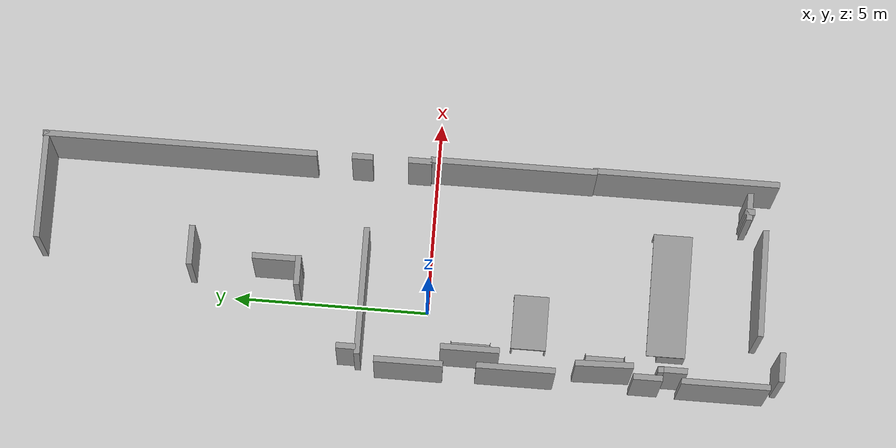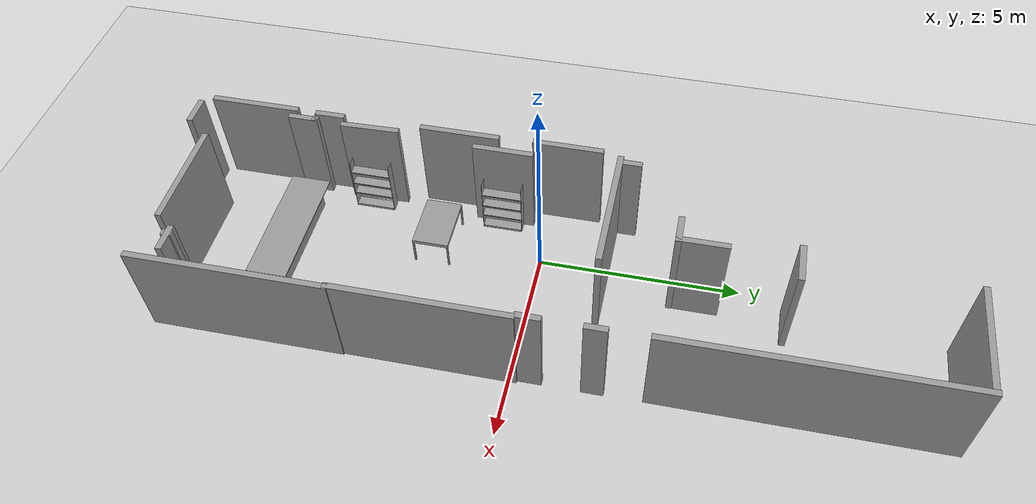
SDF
<sdf version="1.7">
 <world name="default">
  <light name="sun" type="directional">
   <pose>0 0 10 0 -0 0</pose>
   <diffuse>0.8 0.8 0.8 1</diffuse>
   <specular>0.2 0.2 0.2 1</specular>
   <attenuation>
    <range>1000</range>
    <constant>0.9</constant>
    <linear>0.01</linear>
    <quadratic>0.001</quadratic>
   </attenuation>
   <direction>-0.5 0.1 -0.9</direction>
   <spot><inner_angle>0</inner_angle><outer_angle>0</outer_angle><falloff>0</falloff></spot>
  </light>
  <model name="ground_plane">
   <static>1</static>
   <link name="link">
    <collision name="collision">
     <geometry><plane><normal>0 0 1</normal><size>100 100</size></plane></geometry>
     <surface>
      <contact><collide_bitmask>65535</collide_bitmask></contact>
      <friction><ode><mu>100</mu><mu2>50</mu2></ode></friction>
     </surface>
    </collision>
    <visual name="visual">
     <cast_shadows>0</cast_shadows>
     <geometry><plane><normal>0 0 1</normal><size>100 100</size></plane></geometry>
     <material>
      <script><uri>file://media/materials/scripts/gazebo.material</uri><name>Gazebo/Grey</name></script>
     </material>
    </visual>
   </link>
  </model>
  <gravity>0 0 -9.8</gravity>
  <magnetic_field>6e-06 2.3e-05 -4.2e-05</magnetic_field>
  <atmosphere type="adiabatic"/>
  <physics type="ode">
   <max_step_size>0.001</max_step_size>
   <real_time_factor>1</real_time_factor>
   <real_time_update_rate>1000</real_time_update_rate>
  </physics>
  <scene><ambient>0.4 0.4 0.4 1</ambient><background>0.7 0.7 0.7 1</background><shadows>1</shadows></scene>
  <spherical_coordinates>
   <surface_model>EARTH_WGS84</surface_model>
   <latitude_deg>0</latitude_deg>
   <longitude_deg>0</longitude_deg>
   <elevation>0</elevation>
   <heading_deg>0</heading_deg>
  </spherical_coordinates>
  <model name="kitchen_island">
   <link name="link_0">
    <inertial>
     <mass>1</mass>
     <inertia>
      <ixx>0.166667</ixx>
      <ixy>0</ixy>
      <ixz>0</ixz>
      <iyy>0.166667</iyy>
      <iyz>0</iyz>
      <izz>0.166667</izz>
     </inertia>
    </inertial>
    <pose>0 0 0.917 0 -0 0</pose>
    <visual name="visual">
     <geometry><box><size>3.18 1 0.028</size></box></geometry>
     <material>
      <lighting>1</lighting>
      <script><uri>file://media/materials/scripts/gazebo.material</uri><name>Gazebo/Grey</name></script>
      <shader type="pixel"><normal_map>__default__</normal_map></shader>
      <ambient>0.3 0.3 0.3 1</ambient>
      <diffuse>0.7 0.7 0.7 1</diffuse>
      <specular>0.01 0.01 0.01 1</specular>
      <emissive>0 0 0 1</emissive>
     </material>
    </visual>
    <collision name="collision">
     <geometry><box><size>3.18 1 0.028</size></box></geometry>
     <surface>
      <friction>
       <ode><mu>1</mu><mu2>1</mu2><fdir1>0 0 0</fdir1><slip1>0</slip1><slip2>0</slip2></ode>
       <torsional>
        <coefficient>1</coefficient>
        <patch_radius>0</patch_radius>
        <surface_radius>0</surface_radius>
        <use_patch_radius>1</use_patch_radius>
        <ode><slip>0</slip></ode>
       </torsional>
      </friction>
      <bounce><restitution_coefficient>0</restitution_coefficient><threshold>1e+06</threshold></bounce>
      <contact>
       <collide_without_contact>0</collide_without_contact>
       <collide_without_contact_bitmask>1</collide_without_contact_bitmask>
       <collide_bitmask>1</collide_bitmask>
       <ode>
        <soft_cfm>0</soft_cfm>
        <soft_erp>0.2</soft_erp>
        <kp>1e+13</kp>
        <kd>1</kd>
        <max_vel>0.01</max_vel>
        <min_depth>0</min_depth>
       </ode>
       <bullet>
        <split_impulse>1</split_impulse>
        <split_impulse_penetration_threshold>-0.01</split_impulse_penetration_threshold>
        <soft_cfm>0</soft_cfm>
        <soft_erp>0.2</soft_erp>
        <kp>1e+13</kp>
        <kd>1</kd>
       </bullet>
      </contact>
     </surface>
    </collision>
   </link>
   <link name="link_1">
    <inertial>
     <mass>1</mass>
     <inertia>
      <ixx>0.166667</ixx>
      <ixy>0</ixy>
      <ixz>0</ixz>
      <iyy>0.166667</iyy>
      <iyz>0</iyz>
      <izz>0.166667</izz>
     </inertia>
    </inertial>
    <pose>1.576 0 0.4515 0 -0 0</pose>
    <visual name="visual">
     <geometry><box><size>0.028 1 0.903</size></box></geometry>
     <material>
      <lighting>1</lighting>
      <script><uri>file://media/materials/scripts/gazebo.material</uri><name>Gazebo/Grey</name></script>
      <shader type="pixel"><normal_map>__default__</normal_map></shader>
      <ambient>0.3 0.3 0.3 1</ambient>
      <diffuse>0.7 0.7 0.7 1</diffuse>
      <specular>0.01 0.01 0.01 1</specular>
      <emissive>0 0 0 1</emissive>
     </material>
    </visual>
    <collision name="collision">
     <geometry><box><size>0.028 1 0.903</size></box></geometry>
     <surface>
      <friction>
       <ode><mu>1</mu><mu2>1</mu2><fdir1>0 0 0</fdir1><slip1>0</slip1><slip2>0</slip2></ode>
       <torsional>
        <coefficient>1</coefficient>
        <patch_radius>0</patch_radius>
        <surface_radius>0</surface_radius>
        <use_patch_radius>1</use_patch_radius>
        <ode><slip>0</slip></ode>
       </torsional>
      </friction>
      <bounce><restitution_coefficient>0</restitution_coefficient><threshold>1e+06</threshold></bounce>
      <contact>
       <collide_without_contact>0</collide_without_contact>
       <collide_without_contact_bitmask>1</collide_without_contact_bitmask>
       <collide_bitmask>1</collide_bitmask>
       <ode>
        <soft_cfm>0</soft_cfm>
        <soft_erp>0.2</soft_erp>
        <kp>1e+13</kp>
        <kd>1</kd>
        <max_vel>0.01</max_vel>
        <min_depth>0</min_depth>
       </ode>
       <bullet>
        <split_impulse>1</split_impulse>
        <split_impulse_penetration_threshold>-0.01</split_impulse_penetration_threshold>
        <soft_cfm>0</soft_cfm>
        <soft_erp>0.2</soft_erp>
        <kp>1e+13</kp>
        <kd>1</kd>
       </bullet>
      </contact>
     </surface>
    </collision>
   </link>
   <link name="link_2">
    <inertial>
     <mass>1</mass>
     <inertia>
      <ixx>0.166667</ixx>
      <ixy>0</ixy>
      <ixz>0</ixz>
      <iyy>0.166667</iyy>
      <iyz>0</iyz>
      <izz>0.166667</izz>
     </inertia>
    </inertial>
    <pose>-0.01 -0.15 0.4515 0 -0 0</pose>
    <visual name="visual">
     <geometry><box><size>3.14 0.7 0.903</size></box></geometry>
     <material>
      <lighting>1</lighting>
      <script><uri>file://media/materials/scripts/gazebo.material</uri><name>Gazebo/Grey</name></script>
      <shader type="pixel"><normal_map>__default__</normal_map></shader>
      <ambient>0.3 0.3 0.3 1</ambient>
      <diffuse>0.7 0.7 0.7 1</diffuse>
      <specular>0.01 0.01 0.01 1</specular>
      <emissive>0 0 0 1</emissive>
     </material>
    </visual>
    <collision name="collision">
     <geometry><box><size>3.14 0.7 0.903</size></box></geometry>
     <surface>
      <friction>
       <ode><mu>1</mu><mu2>1</mu2><fdir1>0 0 0</fdir1><slip1>0</slip1><slip2>0</slip2></ode>
       <torsional>
        <coefficient>1</coefficient>
        <patch_radius>0</patch_radius>
        <surface_radius>0</surface_radius>
        <use_patch_radius>1</use_patch_radius>
        <ode><slip>0</slip></ode>
       </torsional>
      </friction>
      <bounce><restitution_coefficient>0</restitution_coefficient><threshold>1e+06</threshold></bounce>
      <contact>
       <collide_without_contact>0</collide_without_contact>
       <collide_without_contact_bitmask>1</collide_without_contact_bitmask>
       <collide_bitmask>1</collide_bitmask>
       <ode>
        <soft_cfm>0</soft_cfm>
        <soft_erp>0.2</soft_erp>
        <kp>1e+13</kp>
        <kd>1</kd>
        <max_vel>0.01</max_vel>
        <min_depth>0</min_depth>
       </ode>
       <bullet>
        <split_impulse>1</split_impulse>
        <split_impulse_penetration_threshold>-0.01</split_impulse_penetration_threshold>
        <soft_cfm>0</soft_cfm>
        <soft_erp>0.2</soft_erp>
        <kp>1e+13</kp>
        <kd>1</kd>
       </bullet>
      </contact>
     </surface>
    </collision>
   </link>
   <static>1</static>
   <pose>0.779319 -6.16263 0 0 -0 0</pose>
  </model>
  <model name="Bremen">
   <link name="Wall_12">
    <pose>2.00721 -8.46405 0 0 -0 3.14159</pose>
    <visual name="Wall_12_Visual">
     <pose>0 0 1.25 0 -0 0</pose>
     <geometry><box><size>0.690824 0.15 2.5</size></box></geometry>
     <material>
      <script><uri>file://media/materials/scripts/gazebo.material</uri><name>Gazebo/Grey</name></script>
      <ambient>1 1 1 1</ambient>
      <shader type="pixel"/>
     </material>
     <meta><layer>0</layer></meta>
    </visual>
    <collision name="Wall_12_Collision">
     <pose>0 0 1.25 0 -0 0</pose>
     <geometry><box><size>0.690824 0.15 2.5</size></box></geometry>
     <surface>
      <friction>
       <ode><mu>1</mu><mu2>1</mu2><fdir1>0 0 0</fdir1><slip1>0</slip1><slip2>0</slip2></ode>
       <torsional>
        <coefficient>1</coefficient>
        <patch_radius>0</patch_radius>
        <surface_radius>0</surface_radius>
        <use_patch_radius>1</use_patch_radius>
        <ode><slip>0</slip></ode>
       </torsional>
      </friction>
      <bounce><restitution_coefficient>0</restitution_coefficient><threshold>1e+06</threshold></bounce>
      <contact>
       <collide_without_contact>0</collide_without_contact>
       <collide_without_contact_bitmask>1</collide_without_contact_bitmask>
       <collide_bitmask>1</collide_bitmask>
       <ode>
        <soft_cfm>0</soft_cfm>
        <soft_erp>0.2</soft_erp>
        <kp>1e+13</kp>
        <kd>1</kd>
        <max_vel>0.01</max_vel>
        <min_depth>0</min_depth>
       </ode>
       <bullet>
        <split_impulse>1</split_impulse>
        <split_impulse_penetration_threshold>-0.01</split_impulse_penetration_threshold>
        <soft_cfm>0</soft_cfm>
        <soft_erp>0.2</soft_erp>
        <kp>1e+13</kp>
        <kd>1</kd>
       </bullet>
      </contact>
     </surface>
    </collision>
   </link>
   <link name="Wall_17">
    <pose>1.87355 -8.47751 0 0 0 -1.5708</pose>
    <visual name="Wall_17_Visual">
     <pose>0 0 1.25 0 -0 0</pose>
     <geometry><box><size>0.25 0.15 2.5</size></box></geometry>
     <material>
      <script><uri>file://media/materials/scripts/gazebo.material</uri><name>Gazebo/Grey</name></script>
      <ambient>1 1 1 1</ambient>
      <shader type="pixel"/>
     </material>
     <meta><layer>0</layer></meta>
    </visual>
    <collision name="Wall_17_Collision">
     <pose>0 0 1.25 0 -0 0</pose>
     <geometry><box><size>0.25 0.15 2.5</size></box></geometry>
     <surface>
      <friction>
       <ode><mu>1</mu><mu2>1</mu2><fdir1>0 0 0</fdir1><slip1>0</slip1><slip2>0</slip2></ode>
       <torsional>
        <coefficient>1</coefficient>
        <patch_radius>0</patch_radius>
        <surface_radius>0</surface_radius>
        <use_patch_radius>1</use_patch_radius>
        <ode><slip>0</slip></ode>
       </torsional>
      </friction>
      <bounce><restitution_coefficient>0</restitution_coefficient><threshold>1e+06</threshold></bounce>
      <contact>
       <collide_without_contact>0</collide_without_contact>
       <collide_without_contact_bitmask>1</collide_without_contact_bitmask>
       <collide_bitmask>1</collide_bitmask>
       <ode>
        <soft_cfm>0</soft_cfm>
        <soft_erp>0.2</soft_erp>
        <kp>1e+13</kp>
        <kd>1</kd>
        <max_vel>0.01</max_vel>
        <min_depth>0</min_depth>
       </ode>
       <bullet>
        <split_impulse>1</split_impulse>
        <split_impulse_penetration_threshold>-0.01</split_impulse_penetration_threshold>
        <soft_cfm>0</soft_cfm>
        <soft_erp>0.2</soft_erp>
        <kp>1e+13</kp>
        <kd>1</kd>
       </bullet>
      </contact>
     </surface>
    </collision>
   </link>
   <link name="Wall_19">
    <pose>0.062871 -8.91809 0 0 0 -3.13387</pose>
    <visual name="Wall_19_Visual">
     <pose>0 0 1.25 0 -0 0</pose>
     <geometry><box><size>2.72522 0.15 2.5</size></box></geometry>
     <material>
      <script><uri>file://media/materials/scripts/gazebo.material</uri><name>Gazebo/Grey</name></script>
      <ambient>1 1 1 1</ambient>
      <shader type="pixel"/>
     </material>
     <meta><layer>0</layer></meta>
    </visual>
    <collision name="Wall_19_Collision">
     <pose>0 0 1.25 0 -0 0</pose>
     <geometry><box><size>2.72522 0.15 2.5</size></box></geometry>
     <surface>
      <friction>
       <ode><mu>1</mu><mu2>1</mu2><fdir1>0 0 0</fdir1><slip1>0</slip1><slip2>0</slip2></ode>
       <torsional>
        <coefficient>1</coefficient>
        <patch_radius>0</patch_radius>
        <surface_radius>0</surface_radius>
        <use_patch_radius>1</use_patch_radius>
        <ode><slip>0</slip></ode>
       </torsional>
      </friction>
      <bounce><restitution_coefficient>0</restitution_coefficient><threshold>1e+06</threshold></bounce>
      <contact>
       <collide_without_contact>0</collide_without_contact>
       <collide_without_contact_bitmask>1</collide_without_contact_bitmask>
       <collide_bitmask>1</collide_bitmask>
       <ode>
        <soft_cfm>0</soft_cfm>
        <soft_erp>0.2</soft_erp>
        <kp>1e+13</kp>
        <kd>1</kd>
        <max_vel>0.01</max_vel>
        <min_depth>0</min_depth>
       </ode>
       <bullet>
        <split_impulse>1</split_impulse>
        <split_impulse_penetration_threshold>-0.01</split_impulse_penetration_threshold>
        <soft_cfm>0</soft_cfm>
        <soft_erp>0.2</soft_erp>
        <kp>1e+13</kp>
        <kd>1</kd>
       </bullet>
      </contact>
     </surface>
    </collision>
   </link>
   <link name="Wall_22">
    <pose>2.62503 -6.80715 0 0 -0 1.5708</pose>
    <visual name="Wall_22_Visual">
     <pose>0 0 1.25 0 -0 0</pose>
     <geometry><box><size>4.75 0.15 2.5</size></box></geometry>
     <material>
      <script><uri>file://media/materials/scripts/gazebo.material</uri><name>Gazebo/Grey</name></script>
      <ambient>1 1 1 1</ambient>
      <shader type="pixel"/>
     </material>
     <meta><layer>0</layer></meta>
    </visual>
    <collision name="Wall_22_Collision">
     <pose>0 0 1.25 0 -0 0</pose>
     <geometry><box><size>4.75 0.15 2.5</size></box></geometry>
     <surface>
      <friction>
       <ode><mu>1</mu><mu2>1</mu2><fdir1>0 0 0</fdir1><slip1>0</slip1><slip2>0</slip2></ode>
       <torsional>
        <coefficient>1</coefficient>
        <patch_radius>0</patch_radius>
        <surface_radius>0</surface_radius>
        <use_patch_radius>1</use_patch_radius>
        <ode><slip>0</slip></ode>
       </torsional>
      </friction>
      <bounce><restitution_coefficient>0</restitution_coefficient><threshold>1e+06</threshold></bounce>
      <contact>
       <collide_without_contact>0</collide_without_contact>
       <collide_without_contact_bitmask>1</collide_without_contact_bitmask>
       <collide_bitmask>1</collide_bitmask>
       <ode>
        <soft_cfm>0</soft_cfm>
        <soft_erp>0.2</soft_erp>
        <kp>1e+13</kp>
        <kd>1</kd>
        <max_vel>0.01</max_vel>
        <min_depth>0</min_depth>
       </ode>
       <bullet>
        <split_impulse>1</split_impulse>
        <split_impulse_penetration_threshold>-0.01</split_impulse_penetration_threshold>
        <soft_cfm>0</soft_cfm>
        <soft_erp>0.2</soft_erp>
        <kp>1e+13</kp>
        <kd>1</kd>
       </bullet>
      </contact>
     </surface>
    </collision>
   </link>
   <link name="Wall_24">
    <pose>2.59417 -2.42444 0 0 0 -1.5708</pose>
    <visual name="Wall_24_Visual">
     <pose>0 0 1.25 0 -0 0</pose>
     <geometry><box><size>4.25 0.15 2.5</size></box></geometry>
     <material>
      <script><uri>file://media/materials/scripts/gazebo.material</uri><name>Gazebo/Grey</name></script>
      <ambient>1 1 1 1</ambient>
      <shader type="pixel"/>
     </material>
     <meta><layer>0</layer></meta>
    </visual>
    <collision name="Wall_24_Collision">
     <pose>0 0 1.25 0 -0 0</pose>
     <geometry><box><size>4.25 0.15 2.5</size></box></geometry>
     <surface>
      <friction>
       <ode><mu>1</mu><mu2>1</mu2><fdir1>0 0 0</fdir1><slip1>0</slip1><slip2>0</slip2></ode>
       <torsional>
        <coefficient>1</coefficient>
        <patch_radius>0</patch_radius>
        <surface_radius>0</surface_radius>
        <use_patch_radius>1</use_patch_radius>
        <ode><slip>0</slip></ode>
       </torsional>
      </friction>
      <bounce><restitution_coefficient>0</restitution_coefficient><threshold>1e+06</threshold></bounce>
      <contact>
       <collide_without_contact>0</collide_without_contact>
       <collide_without_contact_bitmask>1</collide_without_contact_bitmask>
       <collide_bitmask>1</collide_bitmask>
       <ode>
        <soft_cfm>0</soft_cfm>
        <soft_erp>0.2</soft_erp>
        <kp>1e+13</kp>
        <kd>1</kd>
        <max_vel>0.01</max_vel>
        <min_depth>0</min_depth>
       </ode>
       <bullet>
        <split_impulse>1</split_impulse>
        <split_impulse_penetration_threshold>-0.01</split_impulse_penetration_threshold>
        <soft_cfm>0</soft_cfm>
        <soft_erp>0.2</soft_erp>
        <kp>1e+13</kp>
        <kd>1</kd>
       </bullet>
      </contact>
     </surface>
    </collision>
   </link>
   <link name="Wall_28">
    <pose>2.53799 -0.034106 0 0 -0 1.5708</pose>
    <visual name="Wall_28_Visual">
     <pose>0 0 1.25 0 -0 0</pose>
     <geometry><box><size>0.605036 0.15 2.5</size></box></geometry>
     <material>
      <script><uri>file://media/materials/scripts/gazebo.material</uri><name>Gazebo/Grey</name></script>
      <ambient>1 1 1 1</ambient>
      <shader type="pixel"/>
     </material>
     <meta><layer>0</layer></meta>
    </visual>
    <collision name="Wall_28_Collision">
     <pose>0 0 1.25 0 -0 0</pose>
     <geometry><box><size>0.605036 0.15 2.5</size></box></geometry>
     <surface>
      <friction>
       <ode><mu>1</mu><mu2>1</mu2><fdir1>0 0 0</fdir1><slip1>0</slip1><slip2>0</slip2></ode>
       <torsional>
        <coefficient>1</coefficient>
        <patch_radius>0</patch_radius>
        <surface_radius>0</surface_radius>
        <use_patch_radius>1</use_patch_radius>
        <ode><slip>0</slip></ode>
       </torsional>
      </friction>
      <bounce><restitution_coefficient>0</restitution_coefficient><threshold>1e+06</threshold></bounce>
      <contact>
       <collide_without_contact>0</collide_without_contact>
       <collide_without_contact_bitmask>1</collide_without_contact_bitmask>
       <collide_bitmask>1</collide_bitmask>
       <ode>
        <soft_cfm>0</soft_cfm>
        <soft_erp>0.2</soft_erp>
        <kp>1e+13</kp>
        <kd>1</kd>
        <max_vel>0.01</max_vel>
        <min_depth>0</min_depth>
       </ode>
       <bullet>
        <split_impulse>1</split_impulse>
        <split_impulse_penetration_threshold>-0.01</split_impulse_penetration_threshold>
        <soft_cfm>0</soft_cfm>
        <soft_erp>0.2</soft_erp>
        <kp>1e+13</kp>
        <kd>1</kd>
       </bullet>
      </contact>
     </surface>
    </collision>
   </link>
   <link name="Wall_31">
    <pose>2.53803 1.43445 0 0 -0 1.5708</pose>
    <visual name="Wall_31_Visual">
     <pose>0 0 1.25 0 -0 0</pose>
     <geometry><box><size>0.531772 0.15 2.5</size></box></geometry>
     <material>
      <script><uri>file://media/materials/scripts/gazebo.material</uri><name>Gazebo/Grey</name></script>
      <ambient>1 1 1 1</ambient>
      <shader type="pixel"/>
     </material>
     <meta><layer>0</layer></meta>
    </visual>
    <collision name="Wall_31_Collision">
     <pose>0 0 1.25 0 -0 0</pose>
     <geometry><box><size>0.531772 0.15 2.5</size></box></geometry>
     <surface>
      <friction>
       <ode><mu>1</mu><mu2>1</mu2><fdir1>0 0 0</fdir1><slip1>0</slip1><slip2>0</slip2></ode>
       <torsional>
        <coefficient>1</coefficient>
        <patch_radius>0</patch_radius>
        <surface_radius>0</surface_radius>
        <use_patch_radius>1</use_patch_radius>
        <ode><slip>0</slip></ode>
       </torsional>
      </friction>
      <bounce><restitution_coefficient>0</restitution_coefficient><threshold>1e+06</threshold></bounce>
      <contact>
       <collide_without_contact>0</collide_without_contact>
       <collide_without_contact_bitmask>1</collide_without_contact_bitmask>
       <collide_bitmask>1</collide_bitmask>
       <ode>
        <soft_cfm>0</soft_cfm>
        <soft_erp>0.2</soft_erp>
        <kp>1e+13</kp>
        <kd>1</kd>
        <max_vel>0.01</max_vel>
        <min_depth>0</min_depth>
       </ode>
       <bullet>
        <split_impulse>1</split_impulse>
        <split_impulse_penetration_threshold>-0.01</split_impulse_penetration_threshold>
        <soft_cfm>0</soft_cfm>
        <soft_erp>0.2</soft_erp>
        <kp>1e+13</kp>
        <kd>1</kd>
       </bullet>
      </contact>
     </surface>
    </collision>
   </link>
   <link name="Wall_34">
    <pose>2.52369 6.09553 0 0 -0 1.5708</pose>
    <visual name="Wall_34_Visual">
     <pose>0 0 1.25 0 -0 0</pose>
     <geometry><box><size>7 0.15 2.5</size></box></geometry>
     <material>
      <script><uri>file://media/materials/scripts/gazebo.material</uri><name>Gazebo/Grey</name></script>
      <ambient>1 1 1 1</ambient>
      <shader type="pixel"/>
     </material>
     <meta><layer>0</layer></meta>
    </visual>
    <collision name="Wall_34_Collision">
     <pose>0 0 1.25 0 -0 0</pose>
     <geometry><box><size>7 0.15 2.5</size></box></geometry>
     <surface>
      <friction>
       <ode><mu>1</mu><mu2>1</mu2><fdir1>0 0 0</fdir1><slip1>0</slip1><slip2>0</slip2></ode>
       <torsional>
        <coefficient>1</coefficient>
        <patch_radius>0</patch_radius>
        <surface_radius>0</surface_radius>
        <use_patch_radius>1</use_patch_radius>
        <ode><slip>0</slip></ode>
       </torsional>
      </friction>
      <bounce><restitution_coefficient>0</restitution_coefficient><threshold>1e+06</threshold></bounce>
      <contact>
       <collide_without_contact>0</collide_without_contact>
       <collide_without_contact_bitmask>1</collide_without_contact_bitmask>
       <collide_bitmask>1</collide_bitmask>
       <ode>
        <soft_cfm>0</soft_cfm>
        <soft_erp>0.2</soft_erp>
        <kp>1e+13</kp>
        <kd>1</kd>
        <max_vel>0.01</max_vel>
        <min_depth>0</min_depth>
       </ode>
       <bullet>
        <split_impulse>1</split_impulse>
        <split_impulse_penetration_threshold>-0.01</split_impulse_penetration_threshold>
        <soft_cfm>0</soft_cfm>
        <soft_erp>0.2</soft_erp>
        <kp>1e+13</kp>
        <kd>1</kd>
       </bullet>
      </contact>
     </surface>
    </collision>
   </link>
   <link name="Wall_37">
    <pose>1.19275 9.49861 0 0 -0 0</pose>
    <visual name="Wall_37_Visual">
     <pose>0 0 1.25 0 -0 0</pose>
     <geometry><box><size>2.75 0.15 2.5</size></box></geometry>
     <material>
      <script><uri>file://media/materials/scripts/gazebo.material</uri><name>Gazebo/Grey</name></script>
      <ambient>1 1 1 1</ambient>
      <shader type="pixel"/>
     </material>
     <meta><layer>0</layer></meta>
    </visual>
    <collision name="Wall_37_Collision">
     <pose>0 0 1.25 0 -0 0</pose>
     <geometry><box><size>2.75 0.15 2.5</size></box></geometry>
     <surface>
      <friction>
       <ode><mu>1</mu><mu2>1</mu2><fdir1>0 0 0</fdir1><slip1>0</slip1><slip2>0</slip2></ode>
       <torsional>
        <coefficient>1</coefficient>
        <patch_radius>0</patch_radius>
        <surface_radius>0</surface_radius>
        <use_patch_radius>1</use_patch_radius>
        <ode><slip>0</slip></ode>
       </torsional>
      </friction>
      <bounce><restitution_coefficient>0</restitution_coefficient><threshold>1e+06</threshold></bounce>
      <contact>
       <collide_without_contact>0</collide_without_contact>
       <collide_without_contact_bitmask>1</collide_without_contact_bitmask>
       <collide_bitmask>1</collide_bitmask>
       <ode>
        <soft_cfm>0</soft_cfm>
        <soft_erp>0.2</soft_erp>
        <kp>1e+13</kp>
        <kd>1</kd>
        <max_vel>0.01</max_vel>
        <min_depth>0</min_depth>
       </ode>
       <bullet>
        <split_impulse>1</split_impulse>
        <split_impulse_penetration_threshold>-0.01</split_impulse_penetration_threshold>
        <soft_cfm>0</soft_cfm>
        <soft_erp>0.2</soft_erp>
        <kp>1e+13</kp>
        <kd>1</kd>
       </bullet>
      </contact>
     </surface>
    </collision>
   </link>
   <link name="Wall_40">
    <pose>-0.912236 1.17525 0 0 -0 3.14159</pose>
    <visual name="Wall_40_Visual">
     <pose>0 0 1.25 0 -0 0</pose>
     <geometry><box><size>3.25 0.15 2.5</size></box></geometry>
     <material>
      <script><uri>file://media/materials/scripts/gazebo.material</uri><name>Gazebo/Grey</name></script>
      <ambient>1 1 1 1</ambient>
      <shader type="pixel"/>
     </material>
     <meta><layer>0</layer></meta>
    </visual>
    <collision name="Wall_40_Collision">
     <pose>0 0 1.25 0 -0 0</pose>
     <geometry><box><size>3.25 0.15 2.5</size></box></geometry>
     <surface>
      <friction>
       <ode><mu>1</mu><mu2>1</mu2><fdir1>0 0 0</fdir1><slip1>0</slip1><slip2>0</slip2></ode>
       <torsional>
        <coefficient>1</coefficient>
        <patch_radius>0</patch_radius>
        <surface_radius>0</surface_radius>
        <use_patch_radius>1</use_patch_radius>
        <ode><slip>0</slip></ode>
       </torsional>
      </friction>
      <bounce><restitution_coefficient>0</restitution_coefficient><threshold>1e+06</threshold></bounce>
      <contact>
       <collide_without_contact>0</collide_without_contact>
       <collide_without_contact_bitmask>1</collide_without_contact_bitmask>
       <collide_bitmask>1</collide_bitmask>
       <ode>
        <soft_cfm>0</soft_cfm>
        <soft_erp>0.2</soft_erp>
        <kp>1e+13</kp>
        <kd>1</kd>
        <max_vel>0.01</max_vel>
        <min_depth>0</min_depth>
       </ode>
       <bullet>
        <split_impulse>1</split_impulse>
        <split_impulse_penetration_threshold>-0.01</split_impulse_penetration_threshold>
        <soft_cfm>0</soft_cfm>
        <soft_erp>0.2</soft_erp>
        <kp>1e+13</kp>
        <kd>1</kd>
       </bullet>
      </contact>
     </surface>
    </collision>
   </link>
   <link name="Wall_42">
    <pose>-2.35817 1.46547 0 0 -0 1.5708</pose>
    <visual name="Wall_42_Visual">
     <pose>0 0 1.25 0 -0 0</pose>
     <geometry><box><size>0.5 0.15 2.5</size></box></geometry>
     <material>
      <script><uri>file://media/materials/scripts/gazebo.material</uri><name>Gazebo/Grey</name></script>
      <ambient>1 1 1 1</ambient>
      <shader type="pixel"/>
     </material>
     <meta><layer>0</layer></meta>
    </visual>
    <collision name="Wall_42_Collision">
     <pose>0 0 1.25 0 -0 0</pose>
     <geometry><box><size>0.5 0.15 2.5</size></box></geometry>
     <surface>
      <friction>
       <ode><mu>1</mu><mu2>1</mu2><fdir1>0 0 0</fdir1><slip1>0</slip1><slip2>0</slip2></ode>
       <torsional>
        <coefficient>1</coefficient>
        <patch_radius>0</patch_radius>
        <surface_radius>0</surface_radius>
        <use_patch_radius>1</use_patch_radius>
        <ode><slip>0</slip></ode>
       </torsional>
      </friction>
      <bounce><restitution_coefficient>0</restitution_coefficient><threshold>1e+06</threshold></bounce>
      <contact>
       <collide_without_contact>0</collide_without_contact>
       <collide_without_contact_bitmask>1</collide_without_contact_bitmask>
       <collide_bitmask>1</collide_bitmask>
       <ode>
        <soft_cfm>0</soft_cfm>
        <soft_erp>0.2</soft_erp>
        <kp>1e+13</kp>
        <kd>1</kd>
        <max_vel>0.01</max_vel>
        <min_depth>0</min_depth>
       </ode>
       <bullet>
        <split_impulse>1</split_impulse>
        <split_impulse_penetration_threshold>-0.01</split_impulse_penetration_threshold>
        <soft_cfm>0</soft_cfm>
        <soft_erp>0.2</soft_erp>
        <kp>1e+13</kp>
        <kd>1</kd>
       </bullet>
      </contact>
     </surface>
    </collision>
   </link>
   <link name="Wall_44">
    <pose>-2.62503 -0.134545 0 0 0 -1.5708</pose>
    <visual name="Wall_44_Visual">
     <pose>0 0 1.25 0 -0 0</pose>
     <geometry><box><size>1.75 0.15 2.5</size></box></geometry>
     <material>
      <script><uri>file://media/materials/scripts/gazebo.material</uri><name>Gazebo/Grey</name></script>
      <ambient>1 1 1 1</ambient>
      <shader type="pixel"/>
     </material>
     <meta><layer>0</layer></meta>
    </visual>
    <collision name="Wall_44_Collision">
     <pose>0 0 1.25 0 -0 0</pose>
     <geometry><box><size>1.75 0.15 2.5</size></box></geometry>
     <surface>
      <friction>
       <ode><mu>1</mu><mu2>1</mu2><fdir1>0 0 0</fdir1><slip1>0</slip1><slip2>0</slip2></ode>
       <torsional>
        <coefficient>1</coefficient>
        <patch_radius>0</patch_radius>
        <surface_radius>0</surface_radius>
        <use_patch_radius>1</use_patch_radius>
        <ode><slip>0</slip></ode>
       </torsional>
      </friction>
      <bounce><restitution_coefficient>0</restitution_coefficient><threshold>1e+06</threshold></bounce>
      <contact>
       <collide_without_contact>0</collide_without_contact>
       <collide_without_contact_bitmask>1</collide_without_contact_bitmask>
       <collide_bitmask>1</collide_bitmask>
       <ode>
        <soft_cfm>0</soft_cfm>
        <soft_erp>0.2</soft_erp>
        <kp>1e+13</kp>
        <kd>1</kd>
        <max_vel>0.01</max_vel>
        <min_depth>0</min_depth>
       </ode>
       <bullet>
        <split_impulse>1</split_impulse>
        <split_impulse_penetration_threshold>-0.01</split_impulse_penetration_threshold>
        <soft_cfm>0</soft_cfm>
        <soft_erp>0.2</soft_erp>
        <kp>1e+13</kp>
        <kd>1</kd>
       </bullet>
      </contact>
     </surface>
    </collision>
   </link>
   <link name="Wall_47">
    <pose>-2.17683 -1.65592 0 0 0 -1.5708</pose>
    <visual name="Wall_47_Visual">
     <pose>0 0 1.25 0 -0 0</pose>
     <geometry><box><size>1.5 0.15 2.5</size></box></geometry>
     <material>
      <script><uri>file://media/materials/scripts/gazebo.material</uri><name>Gazebo/Grey</name></script>
      <ambient>1 1 1 1</ambient>
      <shader type="pixel"/>
     </material>
     <meta><layer>0</layer></meta>
    </visual>
    <collision name="Wall_47_Collision">
     <pose>0 0 1.25 0 -0 0</pose>
     <geometry><box><size>1.5 0.15 2.5</size></box></geometry>
     <surface>
      <friction>
       <ode><mu>1</mu><mu2>1</mu2><fdir1>0 0 0</fdir1><slip1>0</slip1><slip2>0</slip2></ode>
       <torsional>
        <coefficient>1</coefficient>
        <patch_radius>0</patch_radius>
        <surface_radius>0</surface_radius>
        <use_patch_radius>1</use_patch_radius>
        <ode><slip>0</slip></ode>
       </torsional>
      </friction>
      <bounce><restitution_coefficient>0</restitution_coefficient><threshold>1e+06</threshold></bounce>
      <contact>
       <collide_without_contact>0</collide_without_contact>
       <collide_without_contact_bitmask>1</collide_without_contact_bitmask>
       <collide_bitmask>1</collide_bitmask>
       <ode>
        <soft_cfm>0</soft_cfm>
        <soft_erp>0.2</soft_erp>
        <kp>1e+13</kp>
        <kd>1</kd>
        <max_vel>0.01</max_vel>
        <min_depth>0</min_depth>
       </ode>
       <bullet>
        <split_impulse>1</split_impulse>
        <split_impulse_penetration_threshold>-0.01</split_impulse_penetration_threshold>
        <soft_cfm>0</soft_cfm>
        <soft_erp>0.2</soft_erp>
        <kp>1e+13</kp>
        <kd>1</kd>
       </bullet>
      </contact>
     </surface>
    </collision>
   </link>
   <link name="Wall_52">
    <pose>-2.58227 -2.84419 0 0 -0 1.5708</pose>
    <visual name="Wall_52_Visual">
     <pose>0 0 1.25 0 -0 0</pose>
     <geometry><box><size>2 0.15 2.5</size></box></geometry>
     <material>
      <script><uri>file://media/materials/scripts/gazebo.material</uri><name>Gazebo/Grey</name></script>
      <ambient>1 1 1 1</ambient>
      <shader type="pixel"/>
     </material>
     <meta><layer>0</layer></meta>
    </visual>
    <collision name="Wall_52_Collision">
     <pose>0 0 1.25 0 -0 0</pose>
     <geometry><box><size>2 0.15 2.5</size></box></geometry>
     <surface>
      <friction>
       <ode><mu>1</mu><mu2>1</mu2><fdir1>0 0 0</fdir1><slip1>0</slip1><slip2>0</slip2></ode>
       <torsional>
        <coefficient>1</coefficient>
        <patch_radius>0</patch_radius>
        <surface_radius>0</surface_radius>
        <use_patch_radius>1</use_patch_radius>
        <ode><slip>0</slip></ode>
       </torsional>
      </friction>
      <bounce><restitution_coefficient>0</restitution_coefficient><threshold>1e+06</threshold></bounce>
      <contact>
       <collide_without_contact>0</collide_without_contact>
       <collide_without_contact_bitmask>1</collide_without_contact_bitmask>
       <collide_bitmask>1</collide_bitmask>
       <ode>
        <soft_cfm>0</soft_cfm>
        <soft_erp>0.2</soft_erp>
        <kp>1e+13</kp>
        <kd>1</kd>
        <max_vel>0.01</max_vel>
        <min_depth>0</min_depth>
       </ode>
       <bullet>
        <split_impulse>1</split_impulse>
        <split_impulse_penetration_threshold>-0.01</split_impulse_penetration_threshold>
        <soft_cfm>0</soft_cfm>
        <soft_erp>0.2</soft_erp>
        <kp>1e+13</kp>
        <kd>1</kd>
       </bullet>
      </contact>
     </surface>
    </collision>
   </link>
   <link name="Wall_54">
    <pose>-2.31455 -5.06059 0 0 0 -1.54512</pose>
    <visual name="Wall_54_Visual">
     <pose>0 0 1.25 0 -0 0</pose>
     <geometry><box><size>1.47091 0.15 2.5</size></box></geometry>
     <material>
      <script><uri>file://media/materials/scripts/gazebo.material</uri><name>Gazebo/Grey</name></script>
      <ambient>1 1 1 1</ambient>
      <shader type="pixel"/>
     </material>
     <meta><layer>0</layer></meta>
    </visual>
    <collision name="Wall_54_Collision">
     <pose>0 0 1.25 0 -0 0</pose>
     <geometry><box><size>1.47091 0.15 2.5</size></box></geometry>
     <surface>
      <friction>
       <ode><mu>1</mu><mu2>1</mu2><fdir1>0 0 0</fdir1><slip1>0</slip1><slip2>0</slip2></ode>
       <torsional>
        <coefficient>1</coefficient>
        <patch_radius>0</patch_radius>
        <surface_radius>0</surface_radius>
        <use_patch_radius>1</use_patch_radius>
        <ode><slip>0</slip></ode>
       </torsional>
      </friction>
      <bounce><restitution_coefficient>0</restitution_coefficient><threshold>1e+06</threshold></bounce>
      <contact>
       <collide_without_contact>0</collide_without_contact>
       <collide_without_contact_bitmask>1</collide_without_contact_bitmask>
       <collide_bitmask>1</collide_bitmask>
       <ode>
        <soft_cfm>0</soft_cfm>
        <soft_erp>0.2</soft_erp>
        <kp>1e+13</kp>
        <kd>1</kd>
        <max_vel>0.01</max_vel>
        <min_depth>0</min_depth>
       </ode>
       <bullet>
        <split_impulse>1</split_impulse>
        <split_impulse_penetration_threshold>-0.01</split_impulse_penetration_threshold>
        <soft_cfm>0</soft_cfm>
        <soft_erp>0.2</soft_erp>
        <kp>1e+13</kp>
        <kd>1</kd>
       </bullet>
      </contact>
     </surface>
    </collision>
   </link>
   <link name="Wall_57">
    <pose>-2.56406 -6.17227 0 0 -0 1.5708</pose>
    <visual name="Wall_57_Visual">
     <pose>0 0 1.25 0 -0 0</pose>
     <geometry><box><size>0.75 0.15 2.5</size></box></geometry>
     <material>
      <script><uri>file://media/materials/scripts/gazebo.material</uri><name>Gazebo/Grey</name></script>
      <ambient>1 1 1 1</ambient>
      <shader type="pixel"/>
     </material>
     <meta><layer>0</layer></meta>
    </visual>
    <collision name="Wall_57_Collision">
     <pose>0 0 1.25 0 -0 0</pose>
     <geometry><box><size>0.75 0.15 2.5</size></box></geometry>
     <surface>
      <friction>
       <ode><mu>1</mu><mu2>1</mu2><fdir1>0 0 0</fdir1><slip1>0</slip1><slip2>0</slip2></ode>
       <torsional>
        <coefficient>1</coefficient>
        <patch_radius>0</patch_radius>
        <surface_radius>0</surface_radius>
        <use_patch_radius>1</use_patch_radius>
        <ode><slip>0</slip></ode>
       </torsional>
      </friction>
      <bounce><restitution_coefficient>0</restitution_coefficient><threshold>1e+06</threshold></bounce>
      <contact>
       <collide_without_contact>0</collide_without_contact>
       <collide_without_contact_bitmask>1</collide_without_contact_bitmask>
       <collide_bitmask>1</collide_bitmask>
       <ode>
        <soft_cfm>0</soft_cfm>
        <soft_erp>0.2</soft_erp>
        <kp>1e+13</kp>
        <kd>1</kd>
        <max_vel>0.01</max_vel>
        <min_depth>0</min_depth>
       </ode>
       <bullet>
        <split_impulse>1</split_impulse>
        <split_impulse_penetration_threshold>-0.01</split_impulse_penetration_threshold>
        <soft_cfm>0</soft_cfm>
        <soft_erp>0.2</soft_erp>
        <kp>1e+13</kp>
        <kd>1</kd>
       </bullet>
      </contact>
     </surface>
    </collision>
   </link>
   <link name="Wall_60">
    <pose>-2.34359 -6.48281 0 0 -0 0</pose>
    <visual name="Wall_60_Visual">
     <pose>0 0 1.25 0 -0 0</pose>
     <geometry><box><size>0.15 0.15 2.5</size></box></geometry>
     <material>
      <script><uri>file://media/materials/scripts/gazebo.material</uri><name>Gazebo/Grey</name></script>
      <ambient>1 1 1 1</ambient>
      <shader type="pixel"/>
     </material>
     <meta><layer>0</layer></meta>
    </visual>
    <collision name="Wall_60_Collision">
     <pose>0 0 1.25 0 -0 0</pose>
     <geometry><box><size>0.15 0.15 2.5</size></box></geometry>
     <surface>
      <friction>
       <ode><mu>1</mu><mu2>1</mu2><fdir1>0 0 0</fdir1><slip1>0</slip1><slip2>0</slip2></ode>
       <torsional>
        <coefficient>1</coefficient>
        <patch_radius>0</patch_radius>
        <surface_radius>0</surface_radius>
        <use_patch_radius>1</use_patch_radius>
        <ode><slip>0</slip></ode>
       </torsional>
      </friction>
      <bounce><restitution_coefficient>0</restitution_coefficient><threshold>1e+06</threshold></bounce>
      <contact>
       <collide_without_contact>0</collide_without_contact>
       <collide_without_contact_bitmask>1</collide_without_contact_bitmask>
       <collide_bitmask>1</collide_bitmask>
       <ode>
        <soft_cfm>0</soft_cfm>
        <soft_erp>0.2</soft_erp>
        <kp>1e+13</kp>
        <kd>1</kd>
        <max_vel>0.01</max_vel>
        <min_depth>0</min_depth>
       </ode>
       <bullet>
        <split_impulse>1</split_impulse>
        <split_impulse_penetration_threshold>-0.01</split_impulse_penetration_threshold>
        <soft_cfm>0</soft_cfm>
        <soft_erp>0.2</soft_erp>
        <kp>1e+13</kp>
        <kd>1</kd>
       </bullet>
      </contact>
     </surface>
    </collision>
   </link>
   <link name="Wall_62">
    <pose>-2.33294 -6.77988 0 0 -0 1.56772</pose>
    <visual name="Wall_62_Visual">
     <pose>0 0 1.25 0 -0 0</pose>
     <geometry><box><size>0.751334 0.15 2.5</size></box></geometry>
     <material>
      <script><uri>file://media/materials/scripts/gazebo.material</uri><name>Gazebo/Grey</name></script>
      <ambient>1 1 1 1</ambient>
      <shader type="pixel"/>
     </material>
     <meta><layer>0</layer></meta>
    </visual>
    <collision name="Wall_62_Collision">
     <pose>0 0 1.25 0 -0 0</pose>
     <geometry><box><size>0.751334 0.15 2.5</size></box></geometry>
     <surface>
      <friction>
       <ode><mu>1</mu><mu2>1</mu2><fdir1>0 0 0</fdir1><slip1>0</slip1><slip2>0</slip2></ode>
       <torsional>
        <coefficient>1</coefficient>
        <patch_radius>0</patch_radius>
        <surface_radius>0</surface_radius>
        <use_patch_radius>1</use_patch_radius>
        <ode><slip>0</slip></ode>
       </torsional>
      </friction>
      <bounce><restitution_coefficient>0</restitution_coefficient><threshold>1e+06</threshold></bounce>
      <contact>
       <collide_without_contact>0</collide_without_contact>
       <collide_without_contact_bitmask>1</collide_without_contact_bitmask>
       <collide_bitmask>1</collide_bitmask>
       <ode>
        <soft_cfm>0</soft_cfm>
        <soft_erp>0.2</soft_erp>
        <kp>1e+13</kp>
        <kd>1</kd>
        <max_vel>0.01</max_vel>
        <min_depth>0</min_depth>
       </ode>
       <bullet>
        <split_impulse>1</split_impulse>
        <split_impulse_penetration_threshold>-0.01</split_impulse_penetration_threshold>
        <soft_cfm>0</soft_cfm>
        <soft_erp>0.2</soft_erp>
        <kp>1e+13</kp>
        <kd>1</kd>
       </bullet>
      </contact>
     </surface>
    </collision>
   </link>
   <link name="Wall_65">
    <pose>-2.58366 -8.13911 0 0 0 -1.5708</pose>
    <visual name="Wall_65_Visual">
     <pose>0 0 1.25 0 -0 0</pose>
     <geometry><box><size>2.25 0.15 2.5</size></box></geometry>
     <material>
      <script><uri>file://media/materials/scripts/gazebo.material</uri><name>Gazebo/Grey</name></script>
      <ambient>1 1 1 1</ambient>
      <shader type="pixel"/>
     </material>
     <meta><layer>0</layer></meta>
    </visual>
    <collision name="Wall_65_Collision">
     <pose>0 0 1.25 0 -0 0</pose>
     <geometry><box><size>2.25 0.15 2.5</size></box></geometry>
     <surface>
      <friction>
       <ode><mu>1</mu><mu2>1</mu2><fdir1>0 0 0</fdir1><slip1>0</slip1><slip2>0</slip2></ode>
       <torsional>
        <coefficient>1</coefficient>
        <patch_radius>0</patch_radius>
        <surface_radius>0</surface_radius>
        <use_patch_radius>1</use_patch_radius>
        <ode><slip>0</slip></ode>
       </torsional>
      </friction>
      <bounce><restitution_coefficient>0</restitution_coefficient><threshold>1e+06</threshold></bounce>
      <contact>
       <collide_without_contact>0</collide_without_contact>
       <collide_without_contact_bitmask>1</collide_without_contact_bitmask>
       <collide_bitmask>1</collide_bitmask>
       <ode>
        <soft_cfm>0</soft_cfm>
        <soft_erp>0.2</soft_erp>
        <kp>1e+13</kp>
        <kd>1</kd>
        <max_vel>0.01</max_vel>
        <min_depth>0</min_depth>
       </ode>
       <bullet>
        <split_impulse>1</split_impulse>
        <split_impulse_penetration_threshold>-0.01</split_impulse_penetration_threshold>
        <soft_cfm>0</soft_cfm>
        <soft_erp>0.2</soft_erp>
        <kp>1e+13</kp>
        <kd>1</kd>
       </bullet>
      </contact>
     </surface>
    </collision>
   </link>
   <link name="Wall_67">
    <pose>-2.04311 -9.52053 0 0 -0 0</pose>
    <visual name="Wall_67_Visual">
     <pose>0 0 1.25 0 -0 0</pose>
     <geometry><box><size>0.75 0.15 2.5</size></box></geometry>
     <material>
      <script><uri>file://media/materials/scripts/gazebo.material</uri><name>Gazebo/Grey</name></script>
      <ambient>1 1 1 1</ambient>
      <shader type="pixel"/>
     </material>
     <meta><layer>0</layer></meta>
    </visual>
    <collision name="Wall_67_Collision">
     <pose>0 0 1.25 0 -0 0</pose>
     <geometry><box><size>0.75 0.15 2.5</size></box></geometry>
     <surface>
      <friction>
       <ode><mu>1</mu><mu2>1</mu2><fdir1>0 0 0</fdir1><slip1>0</slip1><slip2>0</slip2></ode>
       <torsional>
        <coefficient>1</coefficient>
        <patch_radius>0</patch_radius>
        <surface_radius>0</surface_radius>
        <use_patch_radius>1</use_patch_radius>
        <ode><slip>0</slip></ode>
       </torsional>
      </friction>
      <bounce><restitution_coefficient>0</restitution_coefficient><threshold>1e+06</threshold></bounce>
      <contact>
       <collide_without_contact>0</collide_without_contact>
       <collide_without_contact_bitmask>1</collide_without_contact_bitmask>
       <collide_bitmask>1</collide_bitmask>
       <ode>
        <soft_cfm>0</soft_cfm>
        <soft_erp>0.2</soft_erp>
        <kp>1e+13</kp>
        <kd>1</kd>
        <max_vel>0.01</max_vel>
        <min_depth>0</min_depth>
       </ode>
       <bullet>
        <split_impulse>1</split_impulse>
        <split_impulse_penetration_threshold>-0.01</split_impulse_penetration_threshold>
        <soft_cfm>0</soft_cfm>
        <soft_erp>0.2</soft_erp>
        <kp>1e+13</kp>
        <kd>1</kd>
       </bullet>
      </contact>
     </surface>
    </collision>
   </link>
   <link name="Wall_70">
    <pose>-0.519411 2.83709 0 0 -0 0</pose>
    <visual name="Wall_70_Visual">
     <pose>0 0 1.25 0 -0 0</pose>
     <geometry><box><size>0.75 0.15 2.5</size></box></geometry>
     <material>
      <script><uri>file://media/materials/scripts/gazebo.material</uri><name>Gazebo/Grey</name></script>
      <ambient>1 1 1 1</ambient>
      <shader type="pixel"/>
     </material>
     <meta><layer>0</layer></meta>
    </visual>
    <collision name="Wall_70_Collision">
     <pose>0 0 1.25 0 -0 0</pose>
     <geometry><box><size>0.75 0.15 2.5</size></box></geometry>
     <surface>
      <friction>
       <ode><mu>1</mu><mu2>1</mu2><fdir1>0 0 0</fdir1><slip1>0</slip1><slip2>0</slip2></ode>
       <torsional>
        <coefficient>1</coefficient>
        <patch_radius>0</patch_radius>
        <surface_radius>0</surface_radius>
        <use_patch_radius>1</use_patch_radius>
        <ode><slip>0</slip></ode>
       </torsional>
      </friction>
      <bounce><restitution_coefficient>0</restitution_coefficient><threshold>1e+06</threshold></bounce>
      <contact>
       <collide_without_contact>0</collide_without_contact>
       <collide_without_contact_bitmask>1</collide_without_contact_bitmask>
       <collide_bitmask>1</collide_bitmask>
       <ode>
        <soft_cfm>0</soft_cfm>
        <soft_erp>0.2</soft_erp>
        <kp>1e+13</kp>
        <kd>1</kd>
        <max_vel>0.01</max_vel>
        <min_depth>0</min_depth>
       </ode>
       <bullet>
        <split_impulse>1</split_impulse>
        <split_impulse_penetration_threshold>-0.01</split_impulse_penetration_threshold>
        <soft_cfm>0</soft_cfm>
        <soft_erp>0.2</soft_erp>
        <kp>1e+13</kp>
        <kd>1</kd>
       </bullet>
      </contact>
     </surface>
    </collision>
   </link>
   <link name="Wall_71">
    <pose>-0.229299 3.38708 0 0 -0 1.5708</pose>
    <visual name="Wall_71_Visual">
     <pose>0 0 1.25 0 -0 0</pose>
     <geometry><box><size>1.25 0.15 2.5</size></box></geometry>
     <material>
      <script><uri>file://media/materials/scripts/gazebo.material</uri><name>Gazebo/Grey</name></script>
      <ambient>1 1 1 1</ambient>
      <shader type="pixel"/>
     </material>
     <meta><layer>0</layer></meta>
    </visual>
    <collision name="Wall_71_Collision">
     <pose>0 0 1.25 0 -0 0</pose>
     <geometry><box><size>1.25 0.15 2.5</size></box></geometry>
     <surface>
      <friction>
       <ode><mu>1</mu><mu2>1</mu2><fdir1>0 0 0</fdir1><slip1>0</slip1><slip2>0</slip2></ode>
       <torsional>
        <coefficient>1</coefficient>
        <patch_radius>0</patch_radius>
        <surface_radius>0</surface_radius>
        <use_patch_radius>1</use_patch_radius>
        <ode><slip>0</slip></ode>
       </torsional>
      </friction>
      <bounce><restitution_coefficient>0</restitution_coefficient><threshold>1e+06</threshold></bounce>
      <contact>
       <collide_without_contact>0</collide_without_contact>
       <collide_without_contact_bitmask>1</collide_without_contact_bitmask>
       <collide_bitmask>1</collide_bitmask>
       <ode>
        <soft_cfm>0</soft_cfm>
        <soft_erp>0.2</soft_erp>
        <kp>1e+13</kp>
        <kd>1</kd>
        <max_vel>0.01</max_vel>
        <min_depth>0</min_depth>
       </ode>
       <bullet>
        <split_impulse>1</split_impulse>
        <split_impulse_penetration_threshold>-0.01</split_impulse_penetration_threshold>
        <soft_cfm>0</soft_cfm>
        <soft_erp>0.2</soft_erp>
        <kp>1e+13</kp>
        <kd>1</kd>
       </bullet>
      </contact>
     </surface>
    </collision>
   </link>
   <link name="Wall_73">
    <pose>-0.078426 5.58572 0 0 -0 3.14159</pose>
    <visual name="Wall_73_Visual">
     <pose>0 0 1.25 0 -0 0</pose>
     <geometry><box><size>1 0.15 2.5</size></box></geometry>
     <material>
      <script><uri>file://media/materials/scripts/gazebo.material</uri><name>Gazebo/Grey</name></script>
      <ambient>1 1 1 1</ambient>
      <shader type="pixel"/>
     </material>
     <meta><layer>0</layer></meta>
    </visual>
    <collision name="Wall_73_Collision">
     <pose>0 0 1.25 0 -0 0</pose>
     <geometry><box><size>1 0.15 2.5</size></box></geometry>
     <surface>
      <friction>
       <ode><mu>1</mu><mu2>1</mu2><fdir1>0 0 0</fdir1><slip1>0</slip1><slip2>0</slip2></ode>
       <torsional>
        <coefficient>1</coefficient>
        <patch_radius>0</patch_radius>
        <surface_radius>0</surface_radius>
        <use_patch_radius>1</use_patch_radius>
        <ode><slip>0</slip></ode>
       </torsional>
      </friction>
      <bounce><restitution_coefficient>0</restitution_coefficient><threshold>1e+06</threshold></bounce>
      <contact>
       <collide_without_contact>0</collide_without_contact>
       <collide_without_contact_bitmask>1</collide_without_contact_bitmask>
       <collide_bitmask>1</collide_bitmask>
       <ode>
        <soft_cfm>0</soft_cfm>
        <soft_erp>0.2</soft_erp>
        <kp>1e+13</kp>
        <kd>1</kd>
        <max_vel>0.01</max_vel>
        <min_depth>0</min_depth>
       </ode>
       <bullet>
        <split_impulse>1</split_impulse>
        <split_impulse_penetration_threshold>-0.01</split_impulse_penetration_threshold>
        <soft_cfm>0</soft_cfm>
        <soft_erp>0.2</soft_erp>
        <kp>1e+13</kp>
        <kd>1</kd>
       </bullet>
      </contact>
     </surface>
    </collision>
   </link>
   <static>1</static>
   <pose>0.93134 0.50292 0 0 -0 0</pose>
  </model>
  <model name="bremen_table">
   <static>1</static>
   <link name="link_3">
    <inertial>
     <mass>1</mass>
     <inertia>
      <ixx>0.166667</ixx>
      <ixy>0</ixy>
      <ixz>0</ixz>
      <iyy>0.166667</iyy>
      <iyz>0</iyz>
      <izz>0.166667</izz>
     </inertia>
    </inertial>
    <pose>0 0 0.3 0 -0 0</pose>
    <visual name="visual">
     <geometry><box><size>1.4 0.9 0.09</size></box></geometry>
     <material>
      <lighting>1</lighting>
      <script><uri>file://media/materials/scripts/gazebo.material</uri><name>Gazebo/Grey</name></script>
      <shader type="pixel"><normal_map>__default__</normal_map></shader>
      <ambient>0.3 0.3 0.3 1</ambient>
      <diffuse>0.7 0.7 0.7 1</diffuse>
      <specular>0.01 0.01 0.01 1</specular>
      <emissive>0 0 0 1</emissive>
     </material>
    </visual>
    <collision name="collision">
     <geometry><box><size>1.4 0.9 0.09</size></box></geometry>
     <surface>
      <friction>
       <ode><mu>1</mu><mu2>1</mu2><fdir1>0 0 0</fdir1><slip1>0</slip1><slip2>0</slip2></ode>
       <torsional>
        <coefficient>1</coefficient>
        <patch_radius>0</patch_radius>
        <surface_radius>0</surface_radius>
        <use_patch_radius>1</use_patch_radius>
        <ode><slip>0</slip></ode>
       </torsional>
      </friction>
      <bounce><restitution_coefficient>0</restitution_coefficient><threshold>1e+06</threshold></bounce>
      <contact>
       <collide_without_contact>0</collide_without_contact>
       <collide_without_contact_bitmask>1</collide_without_contact_bitmask>
       <collide_bitmask>1</collide_bitmask>
       <ode>
        <soft_cfm>0</soft_cfm>
        <soft_erp>0.2</soft_erp>
        <kp>1e+13</kp>
        <kd>1</kd>
        <max_vel>0.01</max_vel>
        <min_depth>0</min_depth>
       </ode>
       <bullet>
        <split_impulse>1</split_impulse>
        <split_impulse_penetration_threshold>-0.01</split_impulse_penetration_threshold>
        <soft_cfm>0</soft_cfm>
        <soft_erp>0.2</soft_erp>
        <kp>1e+13</kp>
        <kd>1</kd>
       </bullet>
      </contact>
     </surface>
    </collision>
   </link>
   <link name="link_4">
    <inertial>
     <mass>1</mass>
     <inertia>
      <ixx>0.166667</ixx>
      <ixy>0</ixy>
      <ixz>0</ixz>
      <iyy>0.166667</iyy>
      <iyz>0</iyz>
      <izz>0.166667</izz>
     </inertia>
    </inertial>
    <pose>-0.68 -0.43 -0.075 0 -0 0</pose>
    <visual name="visual">
     <geometry><box><size>0.04 0.04 0.66</size></box></geometry>
     <material>
      <lighting>1</lighting>
      <script><uri>file://media/materials/scripts/gazebo.material</uri><name>Gazebo/Grey</name></script>
      <shader type="pixel"><normal_map>__default__</normal_map></shader>
      <ambient>0.3 0.3 0.3 1</ambient>
      <diffuse>0.7 0.7 0.7 1</diffuse>
      <specular>0.01 0.01 0.01 1</specular>
      <emissive>0 0 0 1</emissive>
     </material>
    </visual>
    <collision name="collision">
     <geometry><box><size>0.04 0.04 0.66</size></box></geometry>
     <surface>
      <friction>
       <ode><mu>1</mu><mu2>1</mu2><fdir1>0 0 0</fdir1><slip1>0</slip1><slip2>0</slip2></ode>
       <torsional>
        <coefficient>1</coefficient>
        <patch_radius>0</patch_radius>
        <surface_radius>0</surface_radius>
        <use_patch_radius>1</use_patch_radius>
        <ode><slip>0</slip></ode>
       </torsional>
      </friction>
      <bounce><restitution_coefficient>0</restitution_coefficient><threshold>1e+06</threshold></bounce>
      <contact>
       <collide_without_contact>0</collide_without_contact>
       <collide_without_contact_bitmask>1</collide_without_contact_bitmask>
       <collide_bitmask>1</collide_bitmask>
       <ode>
        <soft_cfm>0</soft_cfm>
        <soft_erp>0.2</soft_erp>
        <kp>1e+13</kp>
        <kd>1</kd>
        <max_vel>0.01</max_vel>
        <min_depth>0</min_depth>
       </ode>
       <bullet>
        <split_impulse>1</split_impulse>
        <split_impulse_penetration_threshold>-0.01</split_impulse_penetration_threshold>
        <soft_cfm>0</soft_cfm>
        <soft_erp>0.2</soft_erp>
        <kp>1e+13</kp>
        <kd>1</kd>
       </bullet>
      </contact>
     </surface>
    </collision>
   </link>
   <link name="link_4_clone">
    <inertial>
     <mass>1</mass>
     <inertia>
      <ixx>0.166667</ixx>
      <ixy>0</ixy>
      <ixz>0</ixz>
      <iyy>0.166667</iyy>
      <iyz>0</iyz>
      <izz>0.166667</izz>
     </inertia>
    </inertial>
    <pose>-0.68 0.43 -0.075 0 -0 0</pose>
    <visual name="visual">
     <geometry><box><size>0.04 0.04 0.66</size></box></geometry>
     <material>
      <lighting>1</lighting>
      <script><uri>file://media/materials/scripts/gazebo.material</uri><name>Gazebo/Grey</name></script>
      <shader type="pixel"><normal_map>__default__</normal_map></shader>
      <ambient>0.3 0.3 0.3 1</ambient>
      <diffuse>0.7 0.7 0.7 1</diffuse>
      <specular>0.01 0.01 0.01 1</specular>
      <emissive>0 0 0 1</emissive>
     </material>
    </visual>
    <collision name="collision">
     <geometry><box><size>0.04 0.04 0.66</size></box></geometry>
     <surface>
      <friction>
       <ode><mu>1</mu><mu2>1</mu2><fdir1>0 0 0</fdir1><slip1>0</slip1><slip2>0</slip2></ode>
       <torsional>
        <coefficient>1</coefficient>
        <patch_radius>0</patch_radius>
        <surface_radius>0</surface_radius>
        <use_patch_radius>1</use_patch_radius>
        <ode><slip>0</slip></ode>
       </torsional>
      </friction>
      <bounce><restitution_coefficient>0</restitution_coefficient><threshold>1e+06</threshold></bounce>
      <contact>
       <collide_without_contact>0</collide_without_contact>
       <collide_without_contact_bitmask>1</collide_without_contact_bitmask>
       <collide_bitmask>1</collide_bitmask>
       <ode>
        <soft_cfm>0</soft_cfm>
        <soft_erp>0.2</soft_erp>
        <kp>1e+13</kp>
        <kd>1</kd>
        <max_vel>0.01</max_vel>
        <min_depth>0</min_depth>
       </ode>
       <bullet>
        <split_impulse>1</split_impulse>
        <split_impulse_penetration_threshold>-0.01</split_impulse_penetration_threshold>
        <soft_cfm>0</soft_cfm>
        <soft_erp>0.2</soft_erp>
        <kp>1e+13</kp>
        <kd>1</kd>
       </bullet>
      </contact>
     </surface>
    </collision>
   </link>
   <link name="link_4_clone_clone">
    <inertial>
     <mass>1</mass>
     <inertia>
      <ixx>0.166667</ixx>
      <ixy>0</ixy>
      <ixz>0</ixz>
      <iyy>0.166667</iyy>
      <iyz>0</iyz>
      <izz>0.166667</izz>
     </inertia>
    </inertial>
    <pose>0.68 0.43 -0.075 0 -0 0</pose>
    <visual name="visual">
     <geometry><box><size>0.04 0.04 0.66</size></box></geometry>
     <material>
      <lighting>1</lighting>
      <script><uri>file://media/materials/scripts/gazebo.material</uri><name>Gazebo/Grey</name></script>
      <shader type="pixel"><normal_map>__default__</normal_map></shader>
      <ambient>0.3 0.3 0.3 1</ambient>
      <diffuse>0.7 0.7 0.7 1</diffuse>
      <specular>0.01 0.01 0.01 1</specular>
      <emissive>0 0 0 1</emissive>
     </material>
    </visual>
    <collision name="collision">
     <geometry><box><size>0.04 0.04 0.66</size></box></geometry>
     <surface>
      <friction>
       <ode><mu>1</mu><mu2>1</mu2><fdir1>0 0 0</fdir1><slip1>0</slip1><slip2>0</slip2></ode>
       <torsional>
        <coefficient>1</coefficient>
        <patch_radius>0</patch_radius>
        <surface_radius>0</surface_radius>
        <use_patch_radius>1</use_patch_radius>
        <ode><slip>0</slip></ode>
       </torsional>
      </friction>
      <bounce><restitution_coefficient>0</restitution_coefficient><threshold>1e+06</threshold></bounce>
      <contact>
       <collide_without_contact>0</collide_without_contact>
       <collide_without_contact_bitmask>1</collide_without_contact_bitmask>
       <collide_bitmask>1</collide_bitmask>
       <ode>
        <soft_cfm>0</soft_cfm>
        <soft_erp>0.2</soft_erp>
        <kp>1e+13</kp>
        <kd>1</kd>
        <max_vel>0.01</max_vel>
        <min_depth>0</min_depth>
       </ode>
       <bullet>
        <split_impulse>1</split_impulse>
        <split_impulse_penetration_threshold>-0.01</split_impulse_penetration_threshold>
        <soft_cfm>0</soft_cfm>
        <soft_erp>0.2</soft_erp>
        <kp>1e+13</kp>
        <kd>1</kd>
       </bullet>
      </contact>
     </surface>
    </collision>
   </link>
   <link name="link_4_clone_clone_clone">
    <inertial>
     <mass>1</mass>
     <inertia>
      <ixx>0.166667</ixx>
      <ixy>0</ixy>
      <ixz>0</ixz>
      <iyy>0.166667</iyy>
      <iyz>0</iyz>
      <izz>0.166667</izz>
     </inertia>
    </inertial>
    <pose>0.68 -0.43 -0.075 0 -0 0</pose>
    <visual name="visual">
     <geometry><box><size>0.04 0.04 0.66</size></box></geometry>
     <material>
      <lighting>1</lighting>
      <script><uri>file://media/materials/scripts/gazebo.material</uri><name>Gazebo/Grey</name></script>
      <shader type="pixel"><normal_map>__default__</normal_map></shader>
      <ambient>0.3 0.3 0.3 1</ambient>
      <diffuse>0.7 0.7 0.7 1</diffuse>
      <specular>0.01 0.01 0.01 1</specular>
      <emissive>0 0 0 1</emissive>
     </material>
    </visual>
    <collision name="collision">
     <geometry><box><size>0.04 0.04 0.66</size></box></geometry>
     <surface>
      <friction>
       <ode><mu>1</mu><mu2>1</mu2><fdir1>0 0 0</fdir1><slip1>0</slip1><slip2>0</slip2></ode>
       <torsional>
        <coefficient>1</coefficient>
        <patch_radius>0</patch_radius>
        <surface_radius>0</surface_radius>
        <use_patch_radius>1</use_patch_radius>
        <ode><slip>0</slip></ode>
       </torsional>
      </friction>
      <bounce><restitution_coefficient>0</restitution_coefficient><threshold>1e+06</threshold></bounce>
      <contact>
       <collide_without_contact>0</collide_without_contact>
       <collide_without_contact_bitmask>1</collide_without_contact_bitmask>
       <collide_bitmask>1</collide_bitmask>
       <ode>
        <soft_cfm>0</soft_cfm>
        <soft_erp>0.2</soft_erp>
        <kp>1e+13</kp>
        <kd>1</kd>
        <max_vel>0.01</max_vel>
        <min_depth>0</min_depth>
       </ode>
       <bullet>
        <split_impulse>1</split_impulse>
        <split_impulse_penetration_threshold>-0.01</split_impulse_penetration_threshold>
        <soft_cfm>0</soft_cfm>
        <soft_erp>0.2</soft_erp>
        <kp>1e+13</kp>
        <kd>1</kd>
       </bullet>
      </contact>
     </surface>
    </collision>
   </link>
   <static>0</static>
   <pose>-0.159245 -2.65045 0.405 0 -0 0</pose>
  </model>
  <model name="bremen_shelf0_0_clone">
   <link name="link_0">
    <inertial>
     <mass>1</mass>
     <inertia>
      <ixx>0.166667</ixx>
      <ixy>0</ixy>
      <ixz>0</ixz>
      <iyy>0.166667</iyy>
      <iyz>0</iyz>
      <izz>0.166667</izz>
     </inertia>
    </inertial>
    <pose>0 0 -0.639583 0 -0 0</pose>
    <visual name="visual">
     <geometry><box><size>0.99 0.25 0.06</size></box></geometry>
     <material>
      <lighting>1</lighting>
      <script><uri>file://media/materials/scripts/gazebo.material</uri><name>Gazebo/Grey</name></script>
      <shader type="pixel"><normal_map>__default__</normal_map></shader>
      <ambient>0.3 0.3 0.3 1</ambient>
      <diffuse>0.7 0.7 0.7 1</diffuse>
      <specular>0.01 0.01 0.01 1</specular>
      <emissive>0 0 0 1</emissive>
     </material>
    </visual>
    <collision name="collision">
     <geometry><box><size>0.99 0.25 0.06</size></box></geometry>
     <surface>
      <friction>
       <ode><mu>1</mu><mu2>1</mu2><fdir1>0 0 0</fdir1><slip1>0</slip1><slip2>0</slip2></ode>
       <torsional>
        <coefficient>1</coefficient>
        <patch_radius>0</patch_radius>
        <surface_radius>0</surface_radius>
        <use_patch_radius>1</use_patch_radius>
        <ode><slip>0</slip></ode>
       </torsional>
      </friction>
      <bounce><restitution_coefficient>0</restitution_coefficient><threshold>1e+06</threshold></bounce>
      <contact>
       <collide_without_contact>0</collide_without_contact>
       <collide_without_contact_bitmask>1</collide_without_contact_bitmask>
       <collide_bitmask>1</collide_bitmask>
       <ode>
        <soft_cfm>0</soft_cfm>
        <soft_erp>0.2</soft_erp>
        <kp>1e+13</kp>
        <kd>1</kd>
        <max_vel>0.01</max_vel>
        <min_depth>0</min_depth>
       </ode>
       <bullet>
        <split_impulse>1</split_impulse>
        <split_impulse_penetration_threshold>-0.01</split_impulse_penetration_threshold>
        <soft_cfm>0</soft_cfm>
        <soft_erp>0.2</soft_erp>
        <kp>1e+13</kp>
        <kd>1</kd>
       </bullet>
      </contact>
     </surface>
    </collision>
   </link>
   <link name="link_0_clone">
    <inertial>
     <mass>1</mass>
     <inertia>
      <ixx>0.166667</ixx>
      <ixy>0</ixy>
      <ixz>0</ixz>
      <iyy>0.166667</iyy>
      <iyz>0</iyz>
      <izz>0.166667</izz>
     </inertia>
    </inertial>
    <pose>0 0 -0.197083 0 -0 0</pose>
    <visual name="visual">
     <geometry><box><size>0.99 0.25 0.025</size></box></geometry>
     <material>
      <lighting>1</lighting>
      <script><uri>file://media/materials/scripts/gazebo.material</uri><name>Gazebo/Grey</name></script>
      <shader type="pixel"><normal_map>__default__</normal_map></shader>
      <ambient>0.3 0.3 0.3 1</ambient>
      <diffuse>0.7 0.7 0.7 1</diffuse>
      <specular>0.01 0.01 0.01 1</specular>
      <emissive>0 0 0 1</emissive>
     </material>
    </visual>
    <collision name="collision">
     <geometry><box><size>0.99 0.25 0.025</size></box></geometry>
     <surface>
      <friction>
       <ode><mu>1</mu><mu2>1</mu2><fdir1>0 0 0</fdir1><slip1>0</slip1><slip2>0</slip2></ode>
       <torsional>
        <coefficient>1</coefficient>
        <patch_radius>0</patch_radius>
        <surface_radius>0</surface_radius>
        <use_patch_radius>1</use_patch_radius>
        <ode><slip>0</slip></ode>
       </torsional>
      </friction>
      <bounce><restitution_coefficient>0</restitution_coefficient><threshold>1e+06</threshold></bounce>
      <contact>
       <collide_without_contact>0</collide_without_contact>
       <collide_without_contact_bitmask>1</collide_without_contact_bitmask>
       <collide_bitmask>1</collide_bitmask>
       <ode>
        <soft_cfm>0</soft_cfm>
        <soft_erp>0.2</soft_erp>
        <kp>1e+13</kp>
        <kd>1</kd>
        <max_vel>0.01</max_vel>
        <min_depth>0</min_depth>
       </ode>
       <bullet>
        <split_impulse>1</split_impulse>
        <split_impulse_penetration_threshold>-0.01</split_impulse_penetration_threshold>
        <soft_cfm>0</soft_cfm>
        <soft_erp>0.2</soft_erp>
        <kp>1e+13</kp>
        <kd>1</kd>
       </bullet>
      </contact>
     </surface>
    </collision>
   </link>
   <link name="link_0_clone_clone">
    <inertial>
     <mass>1</mass>
     <inertia>
      <ixx>0.166667</ixx>
      <ixy>0</ixy>
      <ixz>0</ixz>
      <iyy>0.166667</iyy>
      <iyz>0</iyz>
      <izz>0.166667</izz>
     </inertia>
    </inertial>
    <pose>0 0 0.147917 0 -0 0</pose>
    <visual name="visual">
     <geometry><box><size>0.99 0.25 0.025</size></box></geometry>
     <material>
      <lighting>1</lighting>
      <script><uri>file://media/materials/scripts/gazebo.material</uri><name>Gazebo/Grey</name></script>
      <shader type="pixel"><normal_map>__default__</normal_map></shader>
      <ambient>0.3 0.3 0.3 1</ambient>
      <diffuse>0.7 0.7 0.7 1</diffuse>
      <specular>0.01 0.01 0.01 1</specular>
      <emissive>0 0 0 1</emissive>
     </material>
    </visual>
    <collision name="collision">
     <geometry><box><size>0.99 0.25 0.025</size></box></geometry>
     <surface>
      <friction>
       <ode><mu>1</mu><mu2>1</mu2><fdir1>0 0 0</fdir1><slip1>0</slip1><slip2>0</slip2></ode>
       <torsional>
        <coefficient>1</coefficient>
        <patch_radius>0</patch_radius>
        <surface_radius>0</surface_radius>
        <use_patch_radius>1</use_patch_radius>
        <ode><slip>0</slip></ode>
       </torsional>
      </friction>
      <bounce><restitution_coefficient>0</restitution_coefficient><threshold>1e+06</threshold></bounce>
      <contact>
       <collide_without_contact>0</collide_without_contact>
       <collide_without_contact_bitmask>1</collide_without_contact_bitmask>
       <collide_bitmask>1</collide_bitmask>
       <ode>
        <soft_cfm>0</soft_cfm>
        <soft_erp>0.2</soft_erp>
        <kp>1e+13</kp>
        <kd>1</kd>
        <max_vel>0.01</max_vel>
        <min_depth>0</min_depth>
       </ode>
       <bullet>
        <split_impulse>1</split_impulse>
        <split_impulse_penetration_threshold>-0.01</split_impulse_penetration_threshold>
        <soft_cfm>0</soft_cfm>
        <soft_erp>0.2</soft_erp>
        <kp>1e+13</kp>
        <kd>1</kd>
       </bullet>
      </contact>
     </surface>
    </collision>
   </link>
   <link name="link_0_clone_clone_clone">
    <inertial>
     <mass>1</mass>
     <inertia>
      <ixx>0.166667</ixx>
      <ixy>0</ixy>
      <ixz>0</ixz>
      <iyy>0.166667</iyy>
      <iyz>0</iyz>
      <izz>0.166667</izz>
     </inertia>
    </inertial>
    <pose>0 0 0.527917 0 -0 0</pose>
    <visual name="visual">
     <geometry><box><size>0.99 0.25 0.025</size></box></geometry>
     <material>
      <lighting>1</lighting>
      <script><uri>file://media/materials/scripts/gazebo.material</uri><name>Gazebo/Grey</name></script>
      <shader type="pixel"><normal_map>__default__</normal_map></shader>
      <ambient>0.3 0.3 0.3 1</ambient>
      <diffuse>0.7 0.7 0.7 1</diffuse>
      <specular>0.01 0.01 0.01 1</specular>
      <emissive>0 0 0 1</emissive>
     </material>
    </visual>
    <collision name="collision">
     <geometry><box><size>0.99 0.25 0.025</size></box></geometry>
     <surface>
      <friction>
       <ode><mu>1</mu><mu2>1</mu2><fdir1>0 0 0</fdir1><slip1>0</slip1><slip2>0</slip2></ode>
       <torsional>
        <coefficient>1</coefficient>
        <patch_radius>0</patch_radius>
        <surface_radius>0</surface_radius>
        <use_patch_radius>1</use_patch_radius>
        <ode><slip>0</slip></ode>
       </torsional>
      </friction>
      <bounce><restitution_coefficient>0</restitution_coefficient><threshold>1e+06</threshold></bounce>
      <contact>
       <collide_without_contact>0</collide_without_contact>
       <collide_without_contact_bitmask>1</collide_without_contact_bitmask>
       <collide_bitmask>1</collide_bitmask>
       <ode>
        <soft_cfm>0</soft_cfm>
        <soft_erp>0.2</soft_erp>
        <kp>1e+13</kp>
        <kd>1</kd>
        <max_vel>0.01</max_vel>
        <min_depth>0</min_depth>
       </ode>
       <bullet>
        <split_impulse>1</split_impulse>
        <split_impulse_penetration_threshold>-0.01</split_impulse_penetration_threshold>
        <soft_cfm>0</soft_cfm>
        <soft_erp>0.2</soft_erp>
        <kp>1e+13</kp>
        <kd>1</kd>
       </bullet>
      </contact>
     </surface>
    </collision>
   </link>
   <link name="link_2">
    <inertial>
     <mass>1</mass>
     <inertia>
      <ixx>0.166667</ixx>
      <ixy>0</ixy>
      <ixz>0</ixz>
      <iyy>0.166667</iyy>
      <iyz>0</iyz>
      <izz>0.166667</izz>
     </inertia>
    </inertial>
    <pose>0.5 0 0.080417 0 -0 0</pose>
    <visual name="visual">
     <geometry><box><size>0.01 0.25 1.5</size></box></geometry>
     <material>
      <lighting>1</lighting>
      <script><uri>file://media/materials/scripts/gazebo.material</uri><name>Gazebo/Grey</name></script>
      <shader type="pixel"><normal_map>__default__</normal_map></shader>
      <ambient>0.3 0.3 0.3 1</ambient>
      <diffuse>0.7 0.7 0.7 1</diffuse>
      <specular>0.01 0.01 0.01 1</specular>
      <emissive>0 0 0 1</emissive>
     </material>
    </visual>
    <collision name="collision">
     <geometry><box><size>0.01 0.25 1.5</size></box></geometry>
     <surface>
      <friction>
       <ode><mu>1</mu><mu2>1</mu2><fdir1>0 0 0</fdir1><slip1>0</slip1><slip2>0</slip2></ode>
       <torsional>
        <coefficient>1</coefficient>
        <patch_radius>0</patch_radius>
        <surface_radius>0</surface_radius>
        <use_patch_radius>1</use_patch_radius>
        <ode><slip>0</slip></ode>
       </torsional>
      </friction>
      <bounce><restitution_coefficient>0</restitution_coefficient><threshold>1e+06</threshold></bounce>
      <contact>
       <collide_without_contact>0</collide_without_contact>
       <collide_without_contact_bitmask>1</collide_without_contact_bitmask>
       <collide_bitmask>1</collide_bitmask>
       <ode>
        <soft_cfm>0</soft_cfm>
        <soft_erp>0.2</soft_erp>
        <kp>1e+13</kp>
        <kd>1</kd>
        <max_vel>0.01</max_vel>
        <min_depth>0</min_depth>
       </ode>
       <bullet>
        <split_impulse>1</split_impulse>
        <split_impulse_penetration_threshold>-0.01</split_impulse_penetration_threshold>
        <soft_cfm>0</soft_cfm>
        <soft_erp>0.2</soft_erp>
        <kp>1e+13</kp>
        <kd>1</kd>
       </bullet>
      </contact>
     </surface>
    </collision>
   </link>
   <link name="link_2_clone">
    <inertial>
     <mass>1</mass>
     <inertia>
      <ixx>0.166667</ixx>
      <ixy>0</ixy>
      <ixz>0</ixz>
      <iyy>0.166667</iyy>
      <iyz>0</iyz>
      <izz>0.166667</izz>
     </inertia>
    </inertial>
    <pose>-0.5 -0 0.080417 0 -0 0</pose>
    <visual name="visual">
     <geometry><box><size>0.01 0.25 1.5</size></box></geometry>
     <material>
      <lighting>1</lighting>
      <script><uri>file://media/materials/scripts/gazebo.material</uri><name>Gazebo/Grey</name></script>
      <shader type="pixel"><normal_map>__default__</normal_map></shader>
      <ambient>0.3 0.3 0.3 1</ambient>
      <diffuse>0.7 0.7 0.7 1</diffuse>
      <specular>0.01 0.01 0.01 1</specular>
      <emissive>0 0 0 1</emissive>
     </material>
    </visual>
    <collision name="collision">
     <geometry><box><size>0.01 0.25 1.5</size></box></geometry>
     <surface>
      <friction>
       <ode><mu>1</mu><mu2>1</mu2><fdir1>0 0 0</fdir1><slip1>0</slip1><slip2>0</slip2></ode>
       <torsional>
        <coefficient>1</coefficient>
        <patch_radius>0</patch_radius>
        <surface_radius>0</surface_radius>
        <use_patch_radius>1</use_patch_radius>
        <ode><slip>0</slip></ode>
       </torsional>
      </friction>
      <bounce><restitution_coefficient>0</restitution_coefficient><threshold>1e+06</threshold></bounce>
      <contact>
       <collide_without_contact>0</collide_without_contact>
       <collide_without_contact_bitmask>1</collide_without_contact_bitmask>
       <collide_bitmask>1</collide_bitmask>
       <ode>
        <soft_cfm>0</soft_cfm>
        <soft_erp>0.2</soft_erp>
        <kp>1e+13</kp>
        <kd>1</kd>
        <max_vel>0.01</max_vel>
        <min_depth>0</min_depth>
       </ode>
       <bullet>
        <split_impulse>1</split_impulse>
        <split_impulse_penetration_threshold>-0.01</split_impulse_penetration_threshold>
        <soft_cfm>0</soft_cfm>
        <soft_erp>0.2</soft_erp>
        <kp>1e+13</kp>
        <kd>1</kd>
       </bullet>
      </contact>
     </surface>
    </collision>
   </link>
   <static>1</static>
   <pose>-1.09959 -4.60089 0.669583 0 -0 1.57079</pose>
  </model>
  <model name="bremen_shelf1">
   <link name="link_0">
    <inertial>
     <mass>1</mass>
     <inertia>
      <ixx>0.166667</ixx>
      <ixy>0</ixy>
      <ixz>0</ixz>
      <iyy>0.166667</iyy>
      <iyz>0</iyz>
      <izz>0.166667</izz>
     </inertia>
    </inertial>
    <pose>0 0 -0.639583 0 -0 0</pose>
    <visual name="visual">
     <geometry><box><size>0.99 0.25 0.06</size></box></geometry>
     <material>
      <lighting>1</lighting>
      <script><uri>file://media/materials/scripts/gazebo.material</uri><name>Gazebo/Grey</name></script>
      <shader type="pixel"><normal_map>__default__</normal_map></shader>
      <ambient>0.3 0.3 0.3 1</ambient>
      <diffuse>0.7 0.7 0.7 1</diffuse>
      <specular>0.01 0.01 0.01 1</specular>
      <emissive>0 0 0 1</emissive>
     </material>
    </visual>
    <collision name="collision">
     <geometry><box><size>0.99 0.25 0.06</size></box></geometry>
     <surface>
      <friction>
       <ode><mu>1</mu><mu2>1</mu2><fdir1>0 0 0</fdir1><slip1>0</slip1><slip2>0</slip2></ode>
       <torsional>
        <coefficient>1</coefficient>
        <patch_radius>0</patch_radius>
        <surface_radius>0</surface_radius>
        <use_patch_radius>1</use_patch_radius>
        <ode><slip>0</slip></ode>
       </torsional>
      </friction>
      <bounce><restitution_coefficient>0</restitution_coefficient><threshold>1e+06</threshold></bounce>
      <contact>
       <collide_without_contact>0</collide_without_contact>
       <collide_without_contact_bitmask>1</collide_without_contact_bitmask>
       <collide_bitmask>1</collide_bitmask>
       <ode>
        <soft_cfm>0</soft_cfm>
        <soft_erp>0.2</soft_erp>
        <kp>1e+13</kp>
        <kd>1</kd>
        <max_vel>0.01</max_vel>
        <min_depth>0</min_depth>
       </ode>
       <bullet>
        <split_impulse>1</split_impulse>
        <split_impulse_penetration_threshold>-0.01</split_impulse_penetration_threshold>
        <soft_cfm>0</soft_cfm>
        <soft_erp>0.2</soft_erp>
        <kp>1e+13</kp>
        <kd>1</kd>
       </bullet>
      </contact>
     </surface>
    </collision>
   </link>
   <link name="link_0_clone">
    <inertial>
     <mass>1</mass>
     <inertia>
      <ixx>0.166667</ixx>
      <ixy>0</ixy>
      <ixz>0</ixz>
      <iyy>0.166667</iyy>
      <iyz>0</iyz>
      <izz>0.166667</izz>
     </inertia>
    </inertial>
    <pose>0 0 -0.227083 0 -0 0</pose>
    <visual name="visual">
     <geometry><box><size>0.99 0.25 0.025</size></box></geometry>
     <material>
      <lighting>1</lighting>
      <script><uri>file://media/materials/scripts/gazebo.material</uri><name>Gazebo/Grey</name></script>
      <shader type="pixel"><normal_map>__default__</normal_map></shader>
      <ambient>0.3 0.3 0.3 1</ambient>
      <diffuse>0.7 0.7 0.7 1</diffuse>
      <specular>0.01 0.01 0.01 1</specular>
      <emissive>0 0 0 1</emissive>
     </material>
    </visual>
    <collision name="collision">
     <geometry><box><size>0.99 0.25 0.025</size></box></geometry>
     <surface>
      <friction>
       <ode><mu>1</mu><mu2>1</mu2><fdir1>0 0 0</fdir1><slip1>0</slip1><slip2>0</slip2></ode>
       <torsional>
        <coefficient>1</coefficient>
        <patch_radius>0</patch_radius>
        <surface_radius>0</surface_radius>
        <use_patch_radius>1</use_patch_radius>
        <ode><slip>0</slip></ode>
       </torsional>
      </friction>
      <bounce><restitution_coefficient>0</restitution_coefficient><threshold>1e+06</threshold></bounce>
      <contact>
       <collide_without_contact>0</collide_without_contact>
       <collide_without_contact_bitmask>1</collide_without_contact_bitmask>
       <collide_bitmask>1</collide_bitmask>
       <ode>
        <soft_cfm>0</soft_cfm>
        <soft_erp>0.2</soft_erp>
        <kp>1e+13</kp>
        <kd>1</kd>
        <max_vel>0.01</max_vel>
        <min_depth>0</min_depth>
       </ode>
       <bullet>
        <split_impulse>1</split_impulse>
        <split_impulse_penetration_threshold>-0.01</split_impulse_penetration_threshold>
        <soft_cfm>0</soft_cfm>
        <soft_erp>0.2</soft_erp>
        <kp>1e+13</kp>
        <kd>1</kd>
       </bullet>
      </contact>
     </surface>
    </collision>
   </link>
   <link name="link_0_clone_clone">
    <inertial>
     <mass>1</mass>
     <inertia>
      <ixx>0.166667</ixx>
      <ixy>0</ixy>
      <ixz>0</ixz>
      <iyy>0.166667</iyy>
      <iyz>0</iyz>
      <izz>0.166667</izz>
     </inertia>
    </inertial>
    <pose>0 0 0.117917 0 -0 0</pose>
    <visual name="visual">
     <geometry><box><size>0.99 0.25 0.025</size></box></geometry>
     <material>
      <lighting>1</lighting>
      <script><uri>file://media/materials/scripts/gazebo.material</uri><name>Gazebo/Grey</name></script>
      <shader type="pixel"><normal_map>__default__</normal_map></shader>
      <ambient>0.3 0.3 0.3 1</ambient>
      <diffuse>0.7 0.7 0.7 1</diffuse>
      <specular>0.01 0.01 0.01 1</specular>
      <emissive>0 0 0 1</emissive>
     </material>
    </visual>
    <collision name="collision">
     <geometry><box><size>0.99 0.25 0.025</size></box></geometry>
     <surface>
      <friction>
       <ode><mu>1</mu><mu2>1</mu2><fdir1>0 0 0</fdir1><slip1>0</slip1><slip2>0</slip2></ode>
       <torsional>
        <coefficient>1</coefficient>
        <patch_radius>0</patch_radius>
        <surface_radius>0</surface_radius>
        <use_patch_radius>1</use_patch_radius>
        <ode><slip>0</slip></ode>
       </torsional>
      </friction>
      <bounce><restitution_coefficient>0</restitution_coefficient><threshold>1e+06</threshold></bounce>
      <contact>
       <collide_without_contact>0</collide_without_contact>
       <collide_without_contact_bitmask>1</collide_without_contact_bitmask>
       <collide_bitmask>1</collide_bitmask>
       <ode>
        <soft_cfm>0</soft_cfm>
        <soft_erp>0.2</soft_erp>
        <kp>1e+13</kp>
        <kd>1</kd>
        <max_vel>0.01</max_vel>
        <min_depth>0</min_depth>
       </ode>
       <bullet>
        <split_impulse>1</split_impulse>
        <split_impulse_penetration_threshold>-0.01</split_impulse_penetration_threshold>
        <soft_cfm>0</soft_cfm>
        <soft_erp>0.2</soft_erp>
        <kp>1e+13</kp>
        <kd>1</kd>
       </bullet>
      </contact>
     </surface>
    </collision>
   </link>
   <link name="link_0_clone_clone_clone">
    <inertial>
     <mass>1</mass>
     <inertia>
      <ixx>0.166667</ixx>
      <ixy>0</ixy>
      <ixz>0</ixz>
      <iyy>0.166667</iyy>
      <iyz>0</iyz>
      <izz>0.166667</izz>
     </inertia>
    </inertial>
    <pose>0 0 0.492917 0 -0 0</pose>
    <visual name="visual">
     <geometry><box><size>0.99 0.25 0.025</size></box></geometry>
     <material>
      <lighting>1</lighting>
      <script><uri>file://media/materials/scripts/gazebo.material</uri><name>Gazebo/Grey</name></script>
      <shader type="pixel"><normal_map>__default__</normal_map></shader>
      <ambient>0.3 0.3 0.3 1</ambient>
      <diffuse>0.7 0.7 0.7 1</diffuse>
      <specular>0.01 0.01 0.01 1</specular>
      <emissive>0 0 0 1</emissive>
     </material>
    </visual>
    <collision name="collision">
     <geometry><box><size>0.99 0.25 0.025</size></box></geometry>
     <surface>
      <friction>
       <ode><mu>1</mu><mu2>1</mu2><fdir1>0 0 0</fdir1><slip1>0</slip1><slip2>0</slip2></ode>
       <torsional>
        <coefficient>1</coefficient>
        <patch_radius>0</patch_radius>
        <surface_radius>0</surface_radius>
        <use_patch_radius>1</use_patch_radius>
        <ode><slip>0</slip></ode>
       </torsional>
      </friction>
      <bounce><restitution_coefficient>0</restitution_coefficient><threshold>1e+06</threshold></bounce>
      <contact>
       <collide_without_contact>0</collide_without_contact>
       <collide_without_contact_bitmask>1</collide_without_contact_bitmask>
       <collide_bitmask>1</collide_bitmask>
       <ode>
        <soft_cfm>0</soft_cfm>
        <soft_erp>0.2</soft_erp>
        <kp>1e+13</kp>
        <kd>1</kd>
        <max_vel>0.01</max_vel>
        <min_depth>0</min_depth>
       </ode>
       <bullet>
        <split_impulse>1</split_impulse>
        <split_impulse_penetration_threshold>-0.01</split_impulse_penetration_threshold>
        <soft_cfm>0</soft_cfm>
        <soft_erp>0.2</soft_erp>
        <kp>1e+13</kp>
        <kd>1</kd>
       </bullet>
      </contact>
     </surface>
    </collision>
   </link>
   <link name="link_2">
    <inertial>
     <mass>1</mass>
     <inertia>
      <ixx>0.166667</ixx>
      <ixy>0</ixy>
      <ixz>0</ixz>
      <iyy>0.166667</iyy>
      <iyz>0</iyz>
      <izz>0.166667</izz>
     </inertia>
    </inertial>
    <pose>0.5 0 0.080417 0 -0 0</pose>
    <visual name="visual">
     <geometry><box><size>0.01 0.25 1.5</size></box></geometry>
     <material>
      <lighting>1</lighting>
      <script><uri>file://media/materials/scripts/gazebo.material</uri><name>Gazebo/Grey</name></script>
      <shader type="pixel"><normal_map>__default__</normal_map></shader>
      <ambient>0.3 0.3 0.3 1</ambient>
      <diffuse>0.7 0.7 0.7 1</diffuse>
      <specular>0.01 0.01 0.01 1</specular>
      <emissive>0 0 0 1</emissive>
     </material>
    </visual>
    <collision name="collision">
     <geometry><box><size>0.01 0.25 1.5</size></box></geometry>
     <surface>
      <friction>
       <ode><mu>1</mu><mu2>1</mu2><fdir1>0 0 0</fdir1><slip1>0</slip1><slip2>0</slip2></ode>
       <torsional>
        <coefficient>1</coefficient>
        <patch_radius>0</patch_radius>
        <surface_radius>0</surface_radius>
        <use_patch_radius>1</use_patch_radius>
        <ode><slip>0</slip></ode>
       </torsional>
      </friction>
      <bounce><restitution_coefficient>0</restitution_coefficient><threshold>1e+06</threshold></bounce>
      <contact>
       <collide_without_contact>0</collide_without_contact>
       <collide_without_contact_bitmask>1</collide_without_contact_bitmask>
       <collide_bitmask>1</collide_bitmask>
       <ode>
        <soft_cfm>0</soft_cfm>
        <soft_erp>0.2</soft_erp>
        <kp>1e+13</kp>
        <kd>1</kd>
        <max_vel>0.01</max_vel>
        <min_depth>0</min_depth>
       </ode>
       <bullet>
        <split_impulse>1</split_impulse>
        <split_impulse_penetration_threshold>-0.01</split_impulse_penetration_threshold>
        <soft_cfm>0</soft_cfm>
        <soft_erp>0.2</soft_erp>
        <kp>1e+13</kp>
        <kd>1</kd>
       </bullet>
      </contact>
     </surface>
    </collision>
   </link>
   <link name="link_2_clone">
    <inertial>
     <mass>1</mass>
     <inertia>
      <ixx>0.166667</ixx>
      <ixy>0</ixy>
      <ixz>0</ixz>
      <iyy>0.166667</iyy>
      <iyz>0</iyz>
      <izz>0.166667</izz>
     </inertia>
    </inertial>
    <pose>-0.5 -0 0.080417 0 -0 0</pose>
    <visual name="visual">
     <geometry><box><size>0.01 0.25 1.5</size></box></geometry>
     <material>
      <lighting>1</lighting>
      <script><uri>file://media/materials/scripts/gazebo.material</uri><name>Gazebo/Grey</name></script>
      <shader type="pixel"><normal_map>__default__</normal_map></shader>
      <ambient>0.3 0.3 0.3 1</ambient>
      <diffuse>0.7 0.7 0.7 1</diffuse>
      <specular>0.01 0.01 0.01 1</specular>
      <emissive>0 0 0 1</emissive>
     </material>
    </visual>
    <collision name="collision">
     <geometry><box><size>0.01 0.25 1.5</size></box></geometry>
     <surface>
      <friction>
       <ode><mu>1</mu><mu2>1</mu2><fdir1>0 0 0</fdir1><slip1>0</slip1><slip2>0</slip2></ode>
       <torsional>
        <coefficient>1</coefficient>
        <patch_radius>0</patch_radius>
        <surface_radius>0</surface_radius>
        <use_patch_radius>1</use_patch_radius>
        <ode><slip>0</slip></ode>
       </torsional>
      </friction>
      <bounce><restitution_coefficient>0</restitution_coefficient><threshold>1e+06</threshold></bounce>
      <contact>
       <collide_without_contact>0</collide_without_contact>
       <collide_without_contact_bitmask>1</collide_without_contact_bitmask>
       <collide_bitmask>1</collide_bitmask>
       <ode>
        <soft_cfm>0</soft_cfm>
        <soft_erp>0.2</soft_erp>
        <kp>1e+13</kp>
        <kd>1</kd>
        <max_vel>0.01</max_vel>
        <min_depth>0</min_depth>
       </ode>
       <bullet>
        <split_impulse>1</split_impulse>
        <split_impulse_penetration_threshold>-0.01</split_impulse_penetration_threshold>
        <soft_cfm>0</soft_cfm>
        <soft_erp>0.2</soft_erp>
        <kp>1e+13</kp>
        <kd>1</kd>
       </bullet>
      </contact>
     </surface>
    </collision>
   </link>
   <static>1</static>
   <pose>-1.02028 -1.16587 0.669583 0 -0 1.57079</pose>
  </model>
  <light name="user_point_light_0" type="point">
   <pose>1.24236 -5.13355 1 0 -0 0</pose>
   <diffuse>0.5 0.5 0.5 1</diffuse>
   <specular>0.1 0.1 0.1 1</specular>
   <attenuation>
    <range>20</range>
    <constant>0.5</constant>
    <linear>0.01</linear>
    <quadratic>0.001</quadratic>
   </attenuation>
   <cast_shadows>0</cast_shadows>
   <direction>0 0 -1</direction>
  </light>
 </world>
</sdf>
